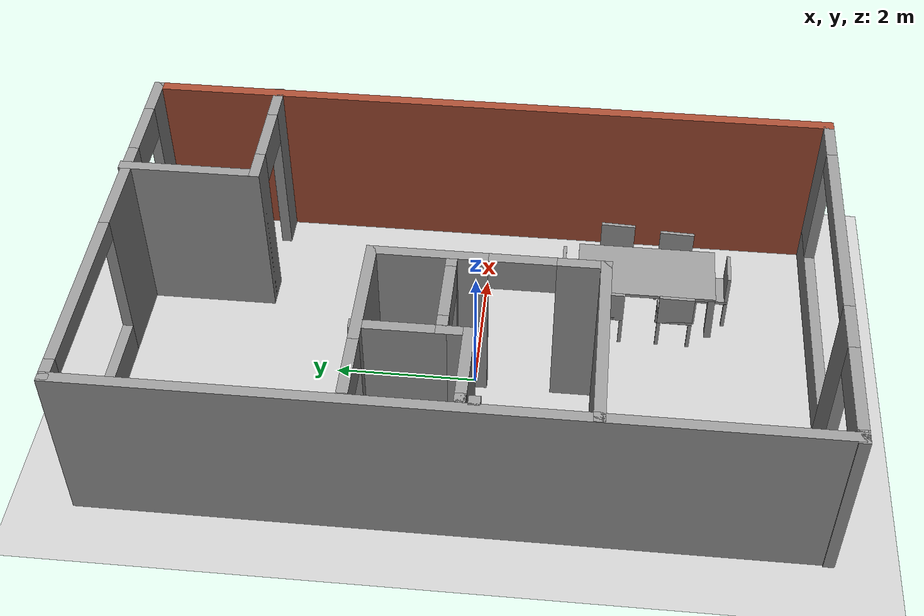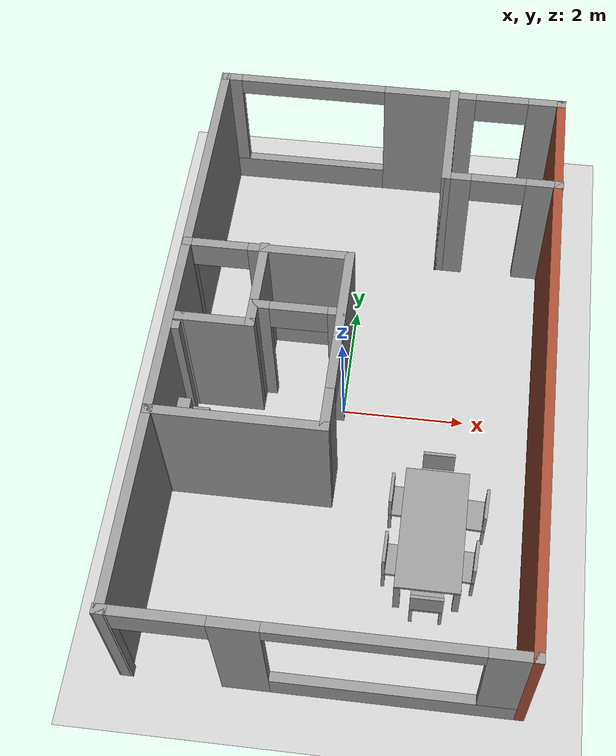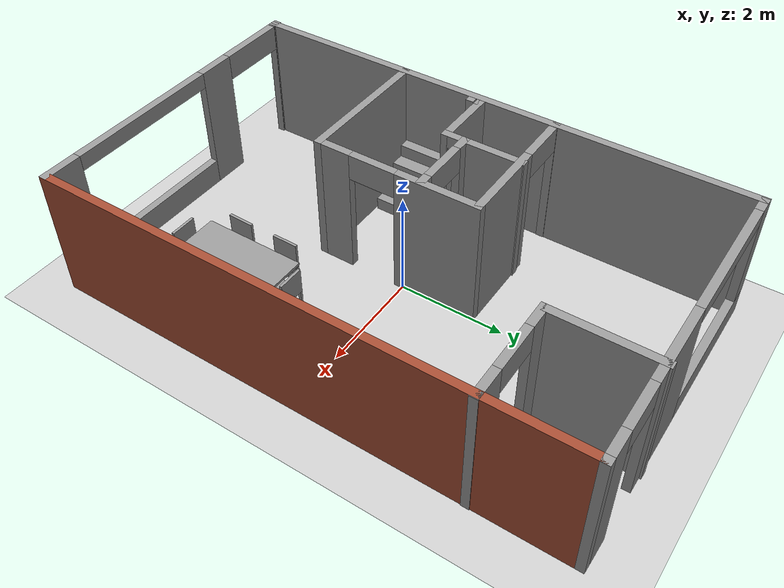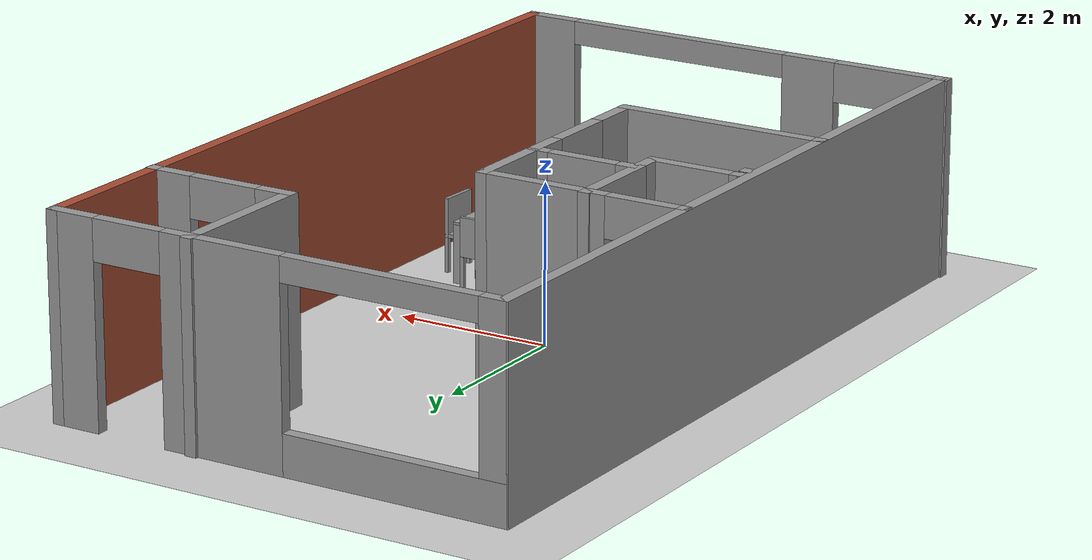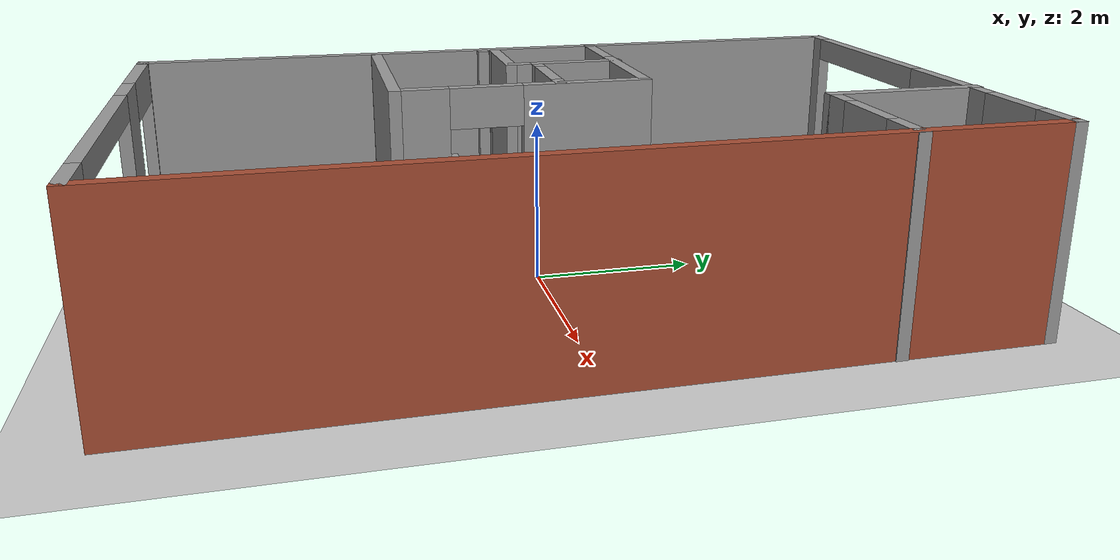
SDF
<sdf version="1.6">
 <world name="default">
  <light name="sun" type="directional">
   <pose>0 0 10 0 -0 0</pose>
   <diffuse>0.8 0.8 0.8 1</diffuse>
   <specular>0.2 0.2 0.2 1</specular>
   <attenuation>
    <range>1000</range>
    <constant>0.9</constant>
    <linear>0.01</linear>
    <quadratic>0.001</quadratic>
   </attenuation>
   <direction>-0.5 0.1 -0.9</direction>
  </light>
  <model name="ground_plane">
   <static>1</static>
   <link name="link">
    <collision name="collision">
     <geometry><plane><normal>0 0 1</normal><size>100 100</size></plane></geometry>
     <surface><friction><ode><mu>100</mu><mu2>50</mu2></ode></friction></surface>
    </collision>
    <visual name="visual">
     <cast_shadows>0</cast_shadows>
     <geometry><plane><normal>0 0 1</normal><size>100 100</size></plane></geometry>
     <material>
      <script><uri>file://media/materials/scripts/gazebo.material</uri><name>Gazebo/Grey</name></script>
     </material>
    </visual>
   </link>
  </model>
  <gravity>0 0 -9.8</gravity>
  <magnetic_field>6e-06 2.3e-05 -4.2e-05</magnetic_field>
  <atmosphere type="adiabatic"/>
  <physics name="default_physics" default="0" type="ode">
   <max_step_size>0.001</max_step_size>
   <real_time_factor>1</real_time_factor>
   <real_time_update_rate>1000</real_time_update_rate>
  </physics>
  <scene><ambient>0.4 0.4 0.4 1</ambient><background>0.7 0.7 0.7 1</background><shadows>1</shadows></scene>
  <spherical_coordinates>
   <surface_model>EARTH_WGS84</surface_model>
   <latitude_deg>0</latitude_deg>
   <longitude_deg>0</longitude_deg>
   <elevation>0</elevation>
   <heading_deg>0</heading_deg>
  </spherical_coordinates>
  <model name="Livingroomlab">
   <pose>0.248675 0.131128 0 0 -0 0</pose>
   <link name="Stairs_1">
    <visual name="Stairs_1_Visual_0">
     <pose>-1.93298 -1.24451 0.125 0 0 -1.5708</pose>
     <geometry><box><size>1 0.2765 0.25</size></box></geometry>
     <material>
      <script><uri>file://media/materials/scripts/gazebo.material</uri><name>Gazebo/Grey</name></script>
      <ambient>1 1 1 1</ambient>
     </material>
     <meta><layer>0</layer></meta>
    </visual>
    <collision name="Stairs_1_Collision_0">
     <geometry><box><size>1 0.2765 0.25</size></box></geometry>
     <pose>-1.93298 -1.24451 0.125 0 0 -1.5708</pose>
    </collision>
    <visual name="Stairs_1_Visual_1">
     <pose>-2.20948 -1.24451 0.375 0 0 -1.5708</pose>
     <geometry><box><size>1 0.2765 0.25</size></box></geometry>
     <material>
      <script><uri>file://media/materials/scripts/gazebo.material</uri><name>Gazebo/Grey</name></script>
      <ambient>1 1 1 1</ambient>
     </material>
     <meta><layer>0</layer></meta>
    </visual>
    <collision name="Stairs_1_Collision_1">
     <geometry><box><size>1 0.2765 0.25</size></box></geometry>
     <pose>-2.20948 -1.24451 0.375 0 0 -1.5708</pose>
    </collision>
    <visual name="Stairs_1_Visual_2">
     <pose>-2.48598 -1.24451 0.625 0 0 -1.5708</pose>
     <geometry><box><size>1 0.2765 0.25</size></box></geometry>
     <material>
      <script><uri>file://media/materials/scripts/gazebo.material</uri><name>Gazebo/Grey</name></script>
      <ambient>1 1 1 1</ambient>
     </material>
     <meta><layer>0</layer></meta>
    </visual>
    <collision name="Stairs_1_Collision_2">
     <geometry><box><size>1 0.2765 0.25</size></box></geometry>
     <pose>-2.48598 -1.24451 0.625 0 0 -1.5708</pose>
    </collision>
    <visual name="Stairs_1_Visual_3">
     <pose>-2.76248 -1.24451 0.875 0 0 -1.5708</pose>
     <geometry><box><size>1 0.2765 0.25</size></box></geometry>
     <material>
      <script><uri>file://media/materials/scripts/gazebo.material</uri><name>Gazebo/Grey</name></script>
      <ambient>1 1 1 1</ambient>
     </material>
     <meta><layer>0</layer></meta>
    </visual>
    <collision name="Stairs_1_Collision_3">
     <geometry><box><size>1 0.2765 0.25</size></box></geometry>
     <pose>-2.76248 -1.24451 0.875 0 0 -1.5708</pose>
    </collision>
   </link>
   <link name="Wall_10">
    <collision name="Wall_10_Collision">
     <geometry><box><size>0.15 0.15 2.5</size></box></geometry>
     <pose>0 0 1.25 0 -0 0</pose>
    </collision>
    <visual name="Wall_10_Visual">
     <pose>0 0 1.25 0 -0 0</pose>
     <geometry><box><size>0.15 0.15 2.5</size></box></geometry>
     <material>
      <script><uri>file://media/materials/scripts/gazebo.material</uri><name>Gazebo/Grey</name></script>
      <ambient>1 1 1 1</ambient>
     </material>
     <meta><layer>0</layer></meta>
    </visual>
    <pose>2.91851 4.90773 0 0 -0 0</pose>
   </link>
   <link name="Wall_15">
    <pose>0.016769 4.90773 0 0 -0 3.14159</pose>
    <visual name="Wall_15_Visual_0">
     <pose>-2.65996 0 1.25 0 -0 0</pose>
     <geometry><box><size>0.633556 0.15 2.5</size></box></geometry>
     <material>
      <script><uri>file://media/materials/scripts/gazebo.material</uri><name>Gazebo/Grey</name></script>
      <ambient>1 1 1 1</ambient>
     </material>
     <meta><layer>0</layer></meta>
    </visual>
    <collision name="Wall_15_Collision_0">
     <geometry><box><size>0.633556 0.15 2.5</size></box></geometry>
     <pose>-2.65996 0 1.25 0 -0 0</pose>
    </collision>
    <visual name="Wall_15_Visual_1">
     <pose>-0.65252 0 1.25 0 -0 0</pose>
     <geometry><box><size>1.58132 0.15 2.5</size></box></geometry>
     <material>
      <script><uri>file://media/materials/scripts/gazebo.material</uri><name>Gazebo/Grey</name></script>
      <ambient>1 1 1 1</ambient>
     </material>
     <meta><layer>0</layer></meta>
    </visual>
    <collision name="Wall_15_Collision_1">
     <geometry><box><size>1.58132 0.15 2.5</size></box></geometry>
     <pose>-0.65252 0 1.25 0 -0 0</pose>
    </collision>
    <visual name="Wall_15_Visual_2">
     <pose>1.55744 0 0.25 0 -0 0</pose>
     <geometry><box><size>2.8386 0.15 0.5</size></box></geometry>
     <material>
      <script><uri>file://media/materials/scripts/gazebo.material</uri><name>Gazebo/Grey</name></script>
      <ambient>1 1 1 1</ambient>
     </material>
     <meta><layer>0</layer></meta>
    </visual>
    <collision name="Wall_15_Collision_2">
     <geometry><box><size>2.8386 0.15 0.5</size></box></geometry>
     <pose>1.55744 0 0.25 0 -0 0</pose>
    </collision>
    <visual name="Wall_15_Visual_3">
     <pose>2.80744 0 1.5 0 -0 0</pose>
     <geometry><box><size>0.338597 0.15 2</size></box></geometry>
     <material>
      <script><uri>file://media/materials/scripts/gazebo.material</uri><name>Gazebo/Grey</name></script>
      <ambient>1 1 1 1</ambient>
     </material>
     <meta><layer>0</layer></meta>
    </visual>
    <collision name="Wall_15_Collision_3">
     <geometry><box><size>0.338597 0.15 2</size></box></geometry>
     <pose>2.80744 0 1.5 0 -0 0</pose>
    </collision>
    <visual name="Wall_15_Visual_4">
     <pose>-1.89318 0 2.25 0 -0 0</pose>
     <geometry><box><size>0.9 0.15 0.5</size></box></geometry>
     <material>
      <script><uri>file://media/materials/scripts/gazebo.material</uri><name>Gazebo/Grey</name></script>
      <ambient>1 1 1 1</ambient>
     </material>
     <meta><layer>0</layer></meta>
    </visual>
    <collision name="Wall_15_Collision_4">
     <geometry><box><size>0.9 0.15 0.5</size></box></geometry>
     <pose>-1.89318 0 2.25 0 -0 0</pose>
    </collision>
    <visual name="Wall_15_Visual_5">
     <pose>1.38814 0 2.35 0 -0 0</pose>
     <geometry><box><size>2.5 0.15 0.3</size></box></geometry>
     <material>
      <script><uri>file://media/materials/scripts/gazebo.material</uri><name>Gazebo/Grey</name></script>
      <ambient>1 1 1 1</ambient>
     </material>
     <meta><layer>0</layer></meta>
    </visual>
    <collision name="Wall_15_Collision_5">
     <geometry><box><size>2.5 0.15 0.3</size></box></geometry>
     <pose>1.38814 0 2.35 0 -0 0</pose>
    </collision>
   </link>
   <link name="Wall_16">
    <collision name="Wall_16_Collision">
     <geometry><box><size>10 0.15 2.5</size></box></geometry>
     <pose>0 0 1.25 0 -0 0</pose>
    </collision>
    <visual name="Wall_16_Visual">
     <pose>0 0 1.25 0 -0 0</pose>
     <geometry><box><size>10 0.15 2.5</size></box></geometry>
     <material>
      <script><uri>file://media/materials/scripts/gazebo.material</uri><name>Gazebo/Grey</name></script>
      <ambient>1 1 1 1</ambient>
     </material>
     <meta><layer>0</layer></meta>
    </visual>
    <pose>-2.90823 -0.017274 0 0 0 -1.5708</pose>
   </link>
   <link name="Wall_17">
    <collision name="Wall_17_Collision">
     <geometry><box><size>0.15 0.15 2.5</size></box></geometry>
     <pose>0 0 1.25 0 -0 0</pose>
    </collision>
    <visual name="Wall_17_Visual">
     <pose>0 0 1.25 0 -0 0</pose>
     <geometry><box><size>0.15 0.15 2.5</size></box></geometry>
     <material>
      <script><uri>file://media/materials/scripts/gazebo.material</uri><name>Gazebo/Grey</name></script>
      <ambient>1 1 1 1</ambient>
     </material>
     <meta><layer>0</layer></meta>
    </visual>
    <pose>-2.88497 -4.94227 0 0 -0 0</pose>
   </link>
   <link name="Wall_19">
    <collision name="Wall_19_Collision">
     <geometry><box><size>2 0.15 2.5</size></box></geometry>
     <pose>0 0 1.25 0 -0 0</pose>
    </collision>
    <visual name="Wall_19_Visual">
     <pose>0 0 1.25 0 -0 0</pose>
     <geometry><box><size>2 0.15 2.5</size></box></geometry>
     <material>
      <script><uri>file://media/materials/scripts/gazebo.material</uri><name>Gazebo/Grey</name></script>
      <ambient>1 1 1 1</ambient>
     </material>
     <meta><layer>0</layer></meta>
    </visual>
    <pose>1.08149 4.01727 0 0 0 -1.5708</pose>
   </link>
   <link name="Wall_20">
    <pose>2.00649 3.09227 0 0 -0 0</pose>
    <visual name="Wall_20_Visual_0">
     <pose>-0.756805 0 1.25 0 -0 0</pose>
     <geometry><box><size>0.48639 0.15 2.5</size></box></geometry>
     <material>
      <script><uri>file://media/materials/scripts/gazebo.material</uri><name>Gazebo/Grey</name></script>
      <ambient>1 1 1 1</ambient>
     </material>
     <meta><layer>0</layer></meta>
    </visual>
    <collision name="Wall_20_Collision_0">
     <geometry><box><size>0.48639 0.15 2.5</size></box></geometry>
     <pose>-0.756805 0 1.25 0 -0 0</pose>
    </collision>
    <visual name="Wall_20_Visual_1">
     <pose>0.693195 0 1.25 0 -0 0</pose>
     <geometry><box><size>0.61361 0.15 2.5</size></box></geometry>
     <material>
      <script><uri>file://media/materials/scripts/gazebo.material</uri><name>Gazebo/Grey</name></script>
      <ambient>1 1 1 1</ambient>
     </material>
     <meta><layer>0</layer></meta>
    </visual>
    <collision name="Wall_20_Collision_1">
     <geometry><box><size>0.61361 0.15 2.5</size></box></geometry>
     <pose>0.693195 0 1.25 0 -0 0</pose>
    </collision>
    <visual name="Wall_20_Visual_2">
     <pose>-0.06361 0 2.25 0 -0 0</pose>
     <geometry><box><size>0.9 0.15 0.5</size></box></geometry>
     <material>
      <script><uri>file://media/materials/scripts/gazebo.material</uri><name>Gazebo/Grey</name></script>
      <ambient>1 1 1 1</ambient>
     </material>
     <meta><layer>0</layer></meta>
    </visual>
    <collision name="Wall_20_Collision_2">
     <geometry><box><size>0.9 0.15 0.5</size></box></geometry>
     <pose>-0.06361 0 2.25 0 -0 0</pose>
    </collision>
   </link>
   <link name="Wall_21">
    <collision name="Wall_21_Collision">
     <geometry><box><size>0.15 0.15 2.5</size></box></geometry>
     <pose>0 0 1.25 0 -0 0</pose>
    </collision>
    <visual name="Wall_21_Visual">
     <pose>0 0 1.25 0 -0 0</pose>
     <geometry><box><size>0.15 0.15 2.5</size></box></geometry>
     <material>
      <script><uri>file://media/materials/scripts/gazebo.material</uri><name>Gazebo/Grey</name></script>
      <ambient>1 1 1 1</ambient>
     </material>
     <meta><layer>0</layer></meta>
    </visual>
    <pose>2.93149 3.09227 0 0 -0 0</pose>
   </link>
   <link name="Wall_23">
    <pose>-1.59731 1.2506 0 0 -0 0</pose>
    <visual name="Wall_23_Visual_0">
     <pose>-1.29946 0 1.25 0 -0 0</pose>
     <geometry><box><size>0.151074 0.15 2.5</size></box></geometry>
     <material>
      <script><uri>file://media/materials/scripts/gazebo.material</uri><name>Gazebo/Grey</name></script>
      <ambient>1 1 1 1</ambient>
     </material>
     <meta><layer>0</layer></meta>
    </visual>
    <collision name="Wall_23_Collision_0">
     <geometry><box><size>0.151074 0.15 2.5</size></box></geometry>
     <pose>-1.29946 0 1.25 0 -0 0</pose>
    </collision>
    <visual name="Wall_23_Visual_1">
     <pose>0.525537 0 1.25 0 -0 0</pose>
     <geometry><box><size>1.69893 0.15 2.5</size></box></geometry>
     <material>
      <script><uri>file://media/materials/scripts/gazebo.material</uri><name>Gazebo/Grey</name></script>
      <ambient>1 1 1 1</ambient>
     </material>
     <meta><layer>0</layer></meta>
    </visual>
    <collision name="Wall_23_Collision_1">
     <geometry><box><size>1.69893 0.15 2.5</size></box></geometry>
     <pose>0.525537 0 1.25 0 -0 0</pose>
    </collision>
    <visual name="Wall_23_Visual_2">
     <pose>-0.773926 0 2.25 0 -0 0</pose>
     <geometry><box><size>0.9 0.15 0.5</size></box></geometry>
     <material>
      <script><uri>file://media/materials/scripts/gazebo.material</uri><name>Gazebo/Grey</name></script>
      <ambient>1 1 1 1</ambient>
     </material>
     <meta><layer>0</layer></meta>
    </visual>
    <collision name="Wall_23_Collision_2">
     <geometry><box><size>0.9 0.15 0.5</size></box></geometry>
     <pose>-0.773926 0 2.25 0 -0 0</pose>
    </collision>
   </link>
   <link name="Wall_26">
    <collision name="Wall_26_Collision">
     <geometry><box><size>0.15 0.15 2.5</size></box></geometry>
     <pose>0 0 1.25 0 -0 0</pose>
    </collision>
    <visual name="Wall_26_Visual">
     <pose>0 0 1.25 0 -0 0</pose>
     <geometry><box><size>0.15 0.15 2.5</size></box></geometry>
     <material>
      <script><uri>file://media/materials/scripts/gazebo.material</uri><name>Gazebo/Grey</name></script>
      <ambient>1 1 1 1</ambient>
     </material>
     <meta><layer>0</layer></meta>
    </visual>
    <pose>-2.78426 -0.349398 0 0 -0 0</pose>
   </link>
   <link name="Wall_28">
    <pose>-0.297309 -0.299398 0 0 0 -1.5708</pose>
    <visual name="Wall_28_Visual_0">
     <pose>-0.81151 0 1.25 0 -0 0</pose>
     <geometry><box><size>1.62698 0.15 2.5</size></box></geometry>
     <material>
      <script><uri>file://media/materials/scripts/gazebo.material</uri><name>Gazebo/Grey</name></script>
      <ambient>1 1 1 1</ambient>
     </material>
     <meta><layer>0</layer></meta>
    </visual>
    <collision name="Wall_28_Collision_0">
     <geometry><box><size>1.62698 0.15 2.5</size></box></geometry>
     <pose>-0.81151 0 1.25 0 -0 0</pose>
    </collision>
    <visual name="Wall_28_Visual_1">
     <pose>1.26349 0 1.25 0 -0 0</pose>
     <geometry><box><size>0.72302 0.15 2.5</size></box></geometry>
     <material>
      <script><uri>file://media/materials/scripts/gazebo.material</uri><name>Gazebo/Grey</name></script>
      <ambient>1 1 1 1</ambient>
     </material>
     <meta><layer>0</layer></meta>
    </visual>
    <collision name="Wall_28_Collision_1">
     <geometry><box><size>0.72302 0.15 2.5</size></box></geometry>
     <pose>1.26349 0 1.25 0 -0 0</pose>
    </collision>
    <visual name="Wall_28_Visual_2">
     <pose>0.45198 0 2.25 0 -0 0</pose>
     <geometry><box><size>0.9 0.15 0.5</size></box></geometry>
     <material>
      <script><uri>file://media/materials/scripts/gazebo.material</uri><name>Gazebo/Grey</name></script>
      <ambient>1 1 1 1</ambient>
     </material>
     <meta><layer>0</layer></meta>
    </visual>
    <collision name="Wall_28_Collision_2">
     <geometry><box><size>0.9 0.15 0.5</size></box></geometry>
     <pose>0.45198 0 2.25 0 -0 0</pose>
    </collision>
   </link>
   <link name="Wall_29">
    <collision name="Wall_29_Collision">
     <geometry><box><size>2.75 0.15 2.5</size></box></geometry>
     <pose>0 0 1.25 0 -0 0</pose>
    </collision>
    <visual name="Wall_29_Visual">
     <pose>0 0 1.25 0 -0 0</pose>
     <geometry><box><size>2.75 0.15 2.5</size></box></geometry>
     <material>
      <script><uri>file://media/materials/scripts/gazebo.material</uri><name>Gazebo/Grey</name></script>
      <ambient>1 1 1 1</ambient>
     </material>
     <meta><layer>0</layer></meta>
    </visual>
    <pose>-1.59731 -1.8494 0 0 -0 3.14159</pose>
   </link>
   <link name="Wall_30">
    <collision name="Wall_30_Collision">
     <geometry><box><size>0.15 0.15 2.5</size></box></geometry>
     <pose>0 0 1.25 0 -0 0</pose>
    </collision>
    <visual name="Wall_30_Visual">
     <pose>0 0 1.25 0 -0 0</pose>
     <geometry><box><size>0.15 0.15 2.5</size></box></geometry>
     <material>
      <script><uri>file://media/materials/scripts/gazebo.material</uri><name>Gazebo/Grey</name></script>
      <ambient>1 1 1 1</ambient>
     </material>
     <meta><layer>0</layer></meta>
    </visual>
    <pose>-2.89731 -1.8494 0 0 -0 0</pose>
   </link>
   <link name="Wall_32">
    <collision name="Wall_32_Collision">
     <geometry><box><size>1.25 0.15 2.5</size></box></geometry>
     <pose>0 0 1.25 0 -0 0</pose>
    </collision>
    <visual name="Wall_32_Visual">
     <pose>0 0 1.25 0 -0 0</pose>
     <geometry><box><size>1.25 0.15 2.5</size></box></geometry>
     <material>
      <script><uri>file://media/materials/scripts/gazebo.material</uri><name>Gazebo/Grey</name></script>
      <ambient>1 1 1 1</ambient>
     </material>
     <meta><layer>0</layer></meta>
    </visual>
    <pose>-1.65945 0.725303 0 0 0 -1.5708</pose>
   </link>
   <link name="Wall_33">
    <pose>-0.984448 0.175303 0 0 -0 0</pose>
    <visual name="Wall_33_Visual_0">
     <pose>-0.587699 0 1.25 0 -0 0</pose>
     <geometry><box><size>0.324602 0.15 2.5</size></box></geometry>
     <material>
      <script><uri>file://media/materials/scripts/gazebo.material</uri><name>Gazebo/Grey</name></script>
      <ambient>1 1 1 1</ambient>
     </material>
     <meta><layer>0</layer></meta>
    </visual>
    <collision name="Wall_33_Collision_0">
     <geometry><box><size>0.324602 0.15 2.5</size></box></geometry>
     <pose>-0.587699 0 1.25 0 -0 0</pose>
    </collision>
    <visual name="Wall_33_Visual_1">
     <pose>0.612301 0 1.25 0 -0 0</pose>
     <geometry><box><size>0.275398 0.15 2.5</size></box></geometry>
     <material>
      <script><uri>file://media/materials/scripts/gazebo.material</uri><name>Gazebo/Grey</name></script>
      <ambient>1 1 1 1</ambient>
     </material>
     <meta><layer>0</layer></meta>
    </visual>
    <collision name="Wall_33_Collision_1">
     <geometry><box><size>0.275398 0.15 2.5</size></box></geometry>
     <pose>0.612301 0 1.25 0 -0 0</pose>
    </collision>
    <visual name="Wall_33_Visual_2">
     <pose>0.024602 0 2.25 0 -0 0</pose>
     <geometry><box><size>0.9 0.15 0.5</size></box></geometry>
     <material>
      <script><uri>file://media/materials/scripts/gazebo.material</uri><name>Gazebo/Grey</name></script>
      <ambient>1 1 1 1</ambient>
     </material>
     <meta><layer>0</layer></meta>
    </visual>
    <collision name="Wall_33_Collision_2">
     <geometry><box><size>0.9 0.15 0.5</size></box></geometry>
     <pose>0.024602 0 2.25 0 -0 0</pose>
    </collision>
   </link>
   <link name="Wall_35">
    <collision name="Wall_35_Collision">
     <geometry><box><size>0.5 0.15 2.5</size></box></geometry>
     <pose>0 0 1.25 0 -0 0</pose>
    </collision>
    <visual name="Wall_35_Visual">
     <pose>0 0 1.25 0 -0 0</pose>
     <geometry><box><size>0.5 0.15 2.5</size></box></geometry>
     <material>
      <script><uri>file://media/materials/scripts/gazebo.material</uri><name>Gazebo/Grey</name></script>
      <ambient>1 1 1 1</ambient>
     </material>
     <meta><layer>0</layer></meta>
    </visual>
    <pose>-1.65945 0.000303 0 0 0 -1.5708</pose>
   </link>
   <link name="Wall_36">
    <collision name="Wall_36_Collision">
     <geometry><box><size>1.25 0.15 2.5</size></box></geometry>
     <pose>0 0 1.25 0 -0 0</pose>
    </collision>
    <visual name="Wall_36_Visual">
     <pose>0 0 1.25 0 -0 0</pose>
     <geometry><box><size>1.25 0.15 2.5</size></box></geometry>
     <material>
      <script><uri>file://media/materials/scripts/gazebo.material</uri><name>Gazebo/Grey</name></script>
      <ambient>1 1 1 1</ambient>
     </material>
     <meta><layer>0</layer></meta>
    </visual>
    <pose>-2.20945 -0.174697 0 0 -0 3.14159</pose>
   </link>
   <link name="Wall_37">
    <collision name="Wall_37_Collision">
     <geometry><box><size>0.15 0.15 2.5</size></box></geometry>
     <pose>0 0 1.25 0 -0 0</pose>
    </collision>
    <visual name="Wall_37_Visual">
     <pose>0 0 1.25 0 -0 0</pose>
     <geometry><box><size>0.15 0.15 2.5</size></box></geometry>
     <material>
      <script><uri>file://media/materials/scripts/gazebo.material</uri><name>Gazebo/Grey</name></script>
      <ambient>1 1 1 1</ambient>
     </material>
     <meta><layer>0</layer></meta>
    </visual>
    <pose>-2.75945 -0.174697 0 0 -0 0</pose>
   </link>
   <link name="Wall_4">
    <pose>-0.006493 -4.94227 0 0 -0 0</pose>
    <visual name="Wall_4_Visual_0">
     <pose>-2.8964 0 1.25 0 -0 0</pose>
     <geometry><box><size>0.207193 0.15 2.5</size></box></geometry>
     <material>
      <script><uri>file://media/materials/scripts/gazebo.material</uri><name>Gazebo/Grey</name></script>
      <ambient>1 1 1 1</ambient>
     </material>
     <meta><layer>0</layer></meta>
    </visual>
    <collision name="Wall_4_Collision_0">
     <geometry><box><size>0.207193 0.15 2.5</size></box></geometry>
     <pose>-2.8964 0 1.25 0 -0 0</pose>
    </collision>
    <visual name="Wall_4_Visual_1">
     <pose>-1.0981 0 1.25 0 -0 0</pose>
     <geometry><box><size>0.722472 0.15 2.5</size></box></geometry>
     <material>
      <script><uri>file://media/materials/scripts/gazebo.material</uri><name>Gazebo/Grey</name></script>
      <ambient>1 1 1 1</ambient>
     </material>
     <meta><layer>0</layer></meta>
    </visual>
    <collision name="Wall_4_Collision_1">
     <geometry><box><size>0.722472 0.15 2.5</size></box></geometry>
     <pose>-1.0981 0 1.25 0 -0 0</pose>
    </collision>
    <visual name="Wall_4_Visual_2">
     <pose>1.13157 0 0.25 0 -0 0</pose>
     <geometry><box><size>3.73686 0.15 0.5</size></box></geometry>
     <material>
      <script><uri>file://media/materials/scripts/gazebo.material</uri><name>Gazebo/Grey</name></script>
      <ambient>1 1 1 1</ambient>
     </material>
     <meta><layer>0</layer></meta>
    </visual>
    <collision name="Wall_4_Collision_2">
     <geometry><box><size>3.73686 0.15 0.5</size></box></geometry>
     <pose>1.13157 0 0.25 0 -0 0</pose>
    </collision>
    <visual name="Wall_4_Visual_3">
     <pose>2.63157 0 1.5 0 -0 0</pose>
     <geometry><box><size>0.736863 0.15 2</size></box></geometry>
     <material>
      <script><uri>file://media/materials/scripts/gazebo.material</uri><name>Gazebo/Grey</name></script>
      <ambient>1 1 1 1</ambient>
     </material>
     <meta><layer>0</layer></meta>
    </visual>
    <collision name="Wall_4_Collision_3">
     <geometry><box><size>0.736863 0.15 2</size></box></geometry>
     <pose>2.63157 0 1.5 0 -0 0</pose>
    </collision>
    <visual name="Wall_4_Visual_4">
     <pose>-2.12607 0 2.25 0 -0 0</pose>
     <geometry><box><size>1.33347 0.15 0.5</size></box></geometry>
     <material>
      <script><uri>file://media/materials/scripts/gazebo.material</uri><name>Gazebo/Grey</name></script>
      <ambient>1 1 1 1</ambient>
     </material>
     <meta><layer>0</layer></meta>
    </visual>
    <collision name="Wall_4_Collision_4">
     <geometry><box><size>1.33347 0.15 0.5</size></box></geometry>
     <pose>-2.12607 0 2.25 0 -0 0</pose>
    </collision>
    <visual name="Wall_4_Visual_5">
     <pose>0.763137 0 2.35 0 -0 0</pose>
     <geometry><box><size>3 0.15 0.3</size></box></geometry>
     <material>
      <script><uri>file://media/materials/scripts/gazebo.material</uri><name>Gazebo/Grey</name></script>
      <ambient>1 1 1 1</ambient>
     </material>
     <meta><layer>0</layer></meta>
    </visual>
    <collision name="Wall_4_Collision_5">
     <geometry><box><size>3 0.15 0.3</size></box></geometry>
     <pose>0.763137 0 2.35 0 -0 0</pose>
    </collision>
   </link>
   <link name="Wall_9">
    <collision name="Wall_9_Collision">
     <geometry><box><size>10 0.15 2.5</size></box></geometry>
     <pose>0 0 1.25 0 -0 0</pose>
    </collision>
    <visual name="Wall_9_Visual">
     <pose>0 0 1.25 0 -0 0</pose>
     <geometry><box><size>10 0.15 2.5</size></box></geometry>
     <material>
      <script><uri>file://media/materials/scripts/gazebo.material</uri><name>Gazebo/Bricks</name></script>
      <ambient>0.996078 0.47451 0.0196078 1</ambient>
     </material>
     <meta><layer>0</layer></meta>
    </visual>
    <pose>2.91851 -0.017274 0 0 -0 1.5708</pose>
   </link>
   <static>1</static>
  </model>
  <model name="table">
   <link name="link_2">
    <pose>-0.000914 0.01077 -0.287764 0 -0 0</pose>
    <inertial>
     <mass>1</mass>
     <inertia>
      <ixx>0.166667</ixx>
      <ixy>0</ixy>
      <ixz>0</ixz>
      <iyy>0.166667</iyy>
      <iyz>0</iyz>
      <izz>0.166667</izz>
     </inertia>
    </inertial>
    <visual name="visual">
     <pose>0 0 0.75 0 -0 0</pose>
     <geometry><box><size>1 2 0.05</size></box></geometry>
     <material>
      <lighting>1</lighting>
      <script><uri>file://media/materials/scripts/gazebo.material</uri><name>Gazebo/Grey</name></script>
      <ambient>0.3 0.3 0.3 1</ambient>
      <diffuse>0.7 0.7 0.7 1</diffuse>
      <specular>0.01 0.01 0.01 1</specular>
      <emissive>0 0 0 1</emissive>
      <shader type="vertex"><normal_map>__default__</normal_map></shader>
     </material>
    </visual>
    <collision name="collision">
     <pose>0 0 0.75 0 -0 0</pose>
     <geometry><box><size>1 2 0.05</size></box></geometry>
     <surface>
      <friction>
       <ode><mu>1</mu><mu2>1</mu2><fdir1>0 0 0</fdir1><slip1>0</slip1><slip2>0</slip2></ode>
       <torsional>
        <coefficient>1</coefficient>
        <patch_radius>0</patch_radius>
        <surface_radius>0</surface_radius>
        <use_patch_radius>1</use_patch_radius>
        <ode><slip>0</slip></ode>
       </torsional>
      </friction>
      <bounce><restitution_coefficient>0</restitution_coefficient><threshold>1e+06</threshold></bounce>
      <contact>
       <collide_without_contact>0</collide_without_contact>
       <collide_without_contact_bitmask>1</collide_without_contact_bitmask>
       <collide_bitmask>1</collide_bitmask>
       <ode>
        <soft_cfm>0</soft_cfm>
        <soft_erp>0.2</soft_erp>
        <kp>1e+13</kp>
        <kd>1</kd>
        <max_vel>0.01</max_vel>
        <min_depth>0</min_depth>
       </ode>
       <bullet>
        <split_impulse>1</split_impulse>
        <split_impulse_penetration_threshold>-0.01</split_impulse_penetration_threshold>
        <soft_cfm>0</soft_cfm>
        <soft_erp>0.2</soft_erp>
        <kp>1e+13</kp>
        <kd>1</kd>
       </bullet>
      </contact>
     </surface>
    </collision>
   </link>
   <link name="link_3">
    <pose>-0.450914 0.87078 0.080236 0 -0 0</pose>
    <inertial>
     <mass>1</mass>
     <inertia>
      <ixx>0.166667</ixx>
      <ixy>0</ixy>
      <ixz>0</ixz>
      <iyy>0.166667</iyy>
      <iyz>0</iyz>
      <izz>0.166667</izz>
     </inertia>
    </inertial>
    <visual name="visual">
     <geometry><box><size>0.1 0.1 0.75</size></box></geometry>
     <material>
      <lighting>1</lighting>
      <script><uri>file://media/materials/scripts/gazebo.material</uri><name>Gazebo/Grey</name></script>
      <ambient>0.3 0.3 0.3 1</ambient>
      <diffuse>0.7 0.7 0.7 1</diffuse>
      <specular>0.01 0.01 0.01 1</specular>
      <emissive>0 0 0 1</emissive>
      <shader type="vertex"><normal_map>__default__</normal_map></shader>
     </material>
    </visual>
    <collision name="collision">
     <geometry><box><size>0.1 0.1 0.75</size></box></geometry>
     <surface>
      <friction>
       <ode><mu>1</mu><mu2>1</mu2><fdir1>0 0 0</fdir1><slip1>0</slip1><slip2>0</slip2></ode>
       <torsional>
        <coefficient>1</coefficient>
        <patch_radius>0</patch_radius>
        <surface_radius>0</surface_radius>
        <use_patch_radius>1</use_patch_radius>
        <ode><slip>0</slip></ode>
       </torsional>
      </friction>
      <bounce><restitution_coefficient>0</restitution_coefficient><threshold>1e+06</threshold></bounce>
      <contact>
       <collide_without_contact>0</collide_without_contact>
       <collide_without_contact_bitmask>1</collide_without_contact_bitmask>
       <collide_bitmask>1</collide_bitmask>
       <ode>
        <soft_cfm>0</soft_cfm>
        <soft_erp>0.2</soft_erp>
        <kp>1e+13</kp>
        <kd>1</kd>
        <max_vel>0.01</max_vel>
        <min_depth>0</min_depth>
       </ode>
       <bullet>
        <split_impulse>1</split_impulse>
        <split_impulse_penetration_threshold>-0.01</split_impulse_penetration_threshold>
        <soft_cfm>0</soft_cfm>
        <soft_erp>0.2</soft_erp>
        <kp>1e+13</kp>
        <kd>1</kd>
       </bullet>
      </contact>
     </surface>
    </collision>
   </link>
   <link name="link_3_clone_0">
    <pose>0.45366 -0.903088 0.047057 0 -0 0</pose>
    <inertial>
     <mass>1</mass>
     <inertia>
      <ixx>0.166667</ixx>
      <ixy>0</ixy>
      <ixz>0</ixz>
      <iyy>0.166667</iyy>
      <iyz>0</iyz>
      <izz>0.166667</izz>
     </inertia>
    </inertial>
    <visual name="visual">
     <geometry><box><size>0.1 0.1 0.75</size></box></geometry>
     <material>
      <lighting>1</lighting>
      <script><uri>file://media/materials/scripts/gazebo.material</uri><name>Gazebo/Grey</name></script>
      <ambient>0.3 0.3 0.3 1</ambient>
      <diffuse>0.7 0.7 0.7 1</diffuse>
      <specular>0.01 0.01 0.01 1</specular>
      <emissive>0 0 0 1</emissive>
      <shader type="vertex"><normal_map>__default__</normal_map></shader>
     </material>
    </visual>
    <collision name="collision">
     <geometry><box><size>0.1 0.1 0.75</size></box></geometry>
     <surface>
      <friction>
       <ode><mu>1</mu><mu2>1</mu2><fdir1>0 0 0</fdir1><slip1>0</slip1><slip2>0</slip2></ode>
       <torsional>
        <coefficient>1</coefficient>
        <patch_radius>0</patch_radius>
        <surface_radius>0</surface_radius>
        <use_patch_radius>1</use_patch_radius>
        <ode><slip>0</slip></ode>
       </torsional>
      </friction>
      <bounce><restitution_coefficient>0</restitution_coefficient><threshold>1e+06</threshold></bounce>
      <contact>
       <collide_without_contact>0</collide_without_contact>
       <collide_without_contact_bitmask>1</collide_without_contact_bitmask>
       <collide_bitmask>1</collide_bitmask>
       <ode>
        <soft_cfm>0</soft_cfm>
        <soft_erp>0.2</soft_erp>
        <kp>1e+13</kp>
        <kd>1</kd>
        <max_vel>0.01</max_vel>
        <min_depth>0</min_depth>
       </ode>
       <bullet>
        <split_impulse>1</split_impulse>
        <split_impulse_penetration_threshold>-0.01</split_impulse_penetration_threshold>
        <soft_cfm>0</soft_cfm>
        <soft_erp>0.2</soft_erp>
        <kp>1e+13</kp>
        <kd>1</kd>
       </bullet>
      </contact>
     </surface>
    </collision>
   </link>
   <link name="link_3_clone_0_clone">
    <pose>-0.450914 -0.93923 0.080236 -0.02 0 0</pose>
    <inertial>
     <mass>1</mass>
     <inertia>
      <ixx>0.166667</ixx>
      <ixy>0</ixy>
      <ixz>0</ixz>
      <iyy>0.166667</iyy>
      <iyz>0</iyz>
      <izz>0.166667</izz>
     </inertia>
    </inertial>
    <visual name="visual">
     <geometry><box><size>0.1 0.1 0.75</size></box></geometry>
     <material>
      <lighting>1</lighting>
      <script><uri>file://media/materials/scripts/gazebo.material</uri><name>Gazebo/Grey</name></script>
      <ambient>0.3 0.3 0.3 1</ambient>
      <diffuse>0.7 0.7 0.7 1</diffuse>
      <specular>0.01 0.01 0.01 1</specular>
      <emissive>0 0 0 1</emissive>
      <shader type="vertex"><normal_map>__default__</normal_map></shader>
     </material>
    </visual>
    <collision name="collision">
     <geometry><box><size>0.1 0.1 0.75</size></box></geometry>
     <surface>
      <friction>
       <ode><mu>1</mu><mu2>1</mu2><fdir1>0 0 0</fdir1><slip1>0</slip1><slip2>0</slip2></ode>
       <torsional>
        <coefficient>1</coefficient>
        <patch_radius>0</patch_radius>
        <surface_radius>0</surface_radius>
        <use_patch_radius>1</use_patch_radius>
        <ode><slip>0</slip></ode>
       </torsional>
      </friction>
      <bounce><restitution_coefficient>0</restitution_coefficient><threshold>1e+06</threshold></bounce>
      <contact>
       <collide_without_contact>0</collide_without_contact>
       <collide_without_contact_bitmask>1</collide_without_contact_bitmask>
       <collide_bitmask>1</collide_bitmask>
       <ode>
        <soft_cfm>0</soft_cfm>
        <soft_erp>0.2</soft_erp>
        <kp>1e+13</kp>
        <kd>1</kd>
        <max_vel>0.01</max_vel>
        <min_depth>0</min_depth>
       </ode>
       <bullet>
        <split_impulse>1</split_impulse>
        <split_impulse_penetration_threshold>-0.01</split_impulse_penetration_threshold>
        <soft_cfm>0</soft_cfm>
        <soft_erp>0.2</soft_erp>
        <kp>1e+13</kp>
        <kd>1</kd>
       </bullet>
      </contact>
     </surface>
    </collision>
   </link>
   <link name="link_3_clone_1">
    <pose>0.449089 0.960775 0.080236 0 -0 0</pose>
    <inertial>
     <mass>1</mass>
     <inertia>
      <ixx>0.166667</ixx>
      <ixy>0</ixy>
      <ixz>0</ixz>
      <iyy>0.166667</iyy>
      <iyz>0</iyz>
      <izz>0.166667</izz>
     </inertia>
    </inertial>
    <visual name="visual">
     <geometry><box><size>0.1 0.1 0.75</size></box></geometry>
     <material>
      <lighting>1</lighting>
      <script><uri>file://media/materials/scripts/gazebo.material</uri><name>Gazebo/Grey</name></script>
      <ambient>0.3 0.3 0.3 1</ambient>
      <diffuse>0.7 0.7 0.7 1</diffuse>
      <specular>0.01 0.01 0.01 1</specular>
      <emissive>0 0 0 1</emissive>
      <shader type="vertex"><normal_map>__default__</normal_map></shader>
     </material>
    </visual>
    <collision name="collision">
     <geometry><box><size>0.1 0.1 0.75</size></box></geometry>
     <surface>
      <friction>
       <ode><mu>1</mu><mu2>1</mu2><fdir1>0 0 0</fdir1><slip1>0</slip1><slip2>0</slip2></ode>
       <torsional>
        <coefficient>1</coefficient>
        <patch_radius>0</patch_radius>
        <surface_radius>0</surface_radius>
        <use_patch_radius>1</use_patch_radius>
        <ode><slip>0</slip></ode>
       </torsional>
      </friction>
      <bounce><restitution_coefficient>0</restitution_coefficient><threshold>1e+06</threshold></bounce>
      <contact>
       <collide_without_contact>0</collide_without_contact>
       <collide_without_contact_bitmask>1</collide_without_contact_bitmask>
       <collide_bitmask>1</collide_bitmask>
       <ode>
        <soft_cfm>0</soft_cfm>
        <soft_erp>0.2</soft_erp>
        <kp>1e+13</kp>
        <kd>1</kd>
        <max_vel>0.01</max_vel>
        <min_depth>0</min_depth>
       </ode>
       <bullet>
        <split_impulse>1</split_impulse>
        <split_impulse_penetration_threshold>-0.01</split_impulse_penetration_threshold>
        <soft_cfm>0</soft_cfm>
        <soft_erp>0.2</soft_erp>
        <kp>1e+13</kp>
        <kd>1</kd>
       </bullet>
      </contact>
     </surface>
    </collision>
   </link>
   <joint name="link_2_JOINT_10" type="fixed">
    <parent>link_2</parent>
    <child>link_3_clone_1</child>
    <physics>
     <ode><limit><cfm>0</cfm><erp>0.2</erp></limit><suspension><cfm>0</cfm><erp>0.2</erp></suspension></ode>
    </physics>
   </joint>
   <joint name="link_2_JOINT_11" type="fixed">
    <parent>link_2</parent>
    <child>link_3</child>
    <physics>
     <ode><limit><cfm>0</cfm><erp>0.2</erp></limit><suspension><cfm>0</cfm><erp>0.2</erp></suspension></ode>
    </physics>
   </joint>
   <joint name="link_2_JOINT_12" type="fixed">
    <parent>link_2</parent>
    <child>link_3_clone_0_clone</child>
    <physics>
     <ode><limit><cfm>0</cfm><erp>0.2</erp></limit><suspension><cfm>0</cfm><erp>0.2</erp></suspension></ode>
    </physics>
   </joint>
   <joint name="link_2_JOINT_8" type="fixed">
    <parent>link_2</parent>
    <child>link_3_clone_0</child>
    <physics>
     <ode><limit><cfm>0</cfm><erp>0.2</erp></limit><suspension><cfm>0</cfm><erp>0.2</erp></suspension></ode>
    </physics>
   </joint>
   <joint name="link_2_JOINT_9" type="fixed">
    <parent>link_2</parent>
    <child>link_3</child>
    <physics>
     <ode><limit><cfm>0</cfm><erp>0.2</erp></limit><suspension><cfm>0</cfm><erp>0.2</erp></suspension></ode>
    </physics>
   </joint>
   <static>0</static>
   <pose>1.66154 -2.36692 0.309262 0 -0 0</pose>
  </model>
  <model name="Chair">
   <link name="link_5">
    <pose>-0.225 0.256445 -0.120833 0 -0 0</pose>
    <inertial>
     <mass>1</mass>
     <inertia>
      <ixx>0.166667</ixx>
      <ixy>0</ixy>
      <ixz>0</ixz>
      <iyy>0.166667</iyy>
      <iyz>0</iyz>
      <izz>0.166667</izz>
     </inertia>
    </inertial>
    <visual name="visual">
     <geometry><box><size>0.05 0.05 0.45</size></box></geometry>
     <material>
      <lighting>1</lighting>
      <script><uri>file://media/materials/scripts/gazebo.material</uri><name>Gazebo/Grey</name></script>
      <ambient>0.3 0.3 0.3 1</ambient>
      <diffuse>0.7 0.7 0.7 1</diffuse>
      <specular>0.01 0.01 0.01 1</specular>
      <emissive>0 0 0 1</emissive>
      <shader type="vertex"><normal_map>__default__</normal_map></shader>
     </material>
    </visual>
    <collision name="collision">
     <geometry><box><size>0.05 0.05 0.45</size></box></geometry>
     <surface>
      <friction>
       <ode><mu>1</mu><mu2>1</mu2><fdir1>0 0 0</fdir1><slip1>0</slip1><slip2>0</slip2></ode>
       <torsional>
        <coefficient>1</coefficient>
        <patch_radius>0</patch_radius>
        <surface_radius>0</surface_radius>
        <use_patch_radius>1</use_patch_radius>
        <ode><slip>0</slip></ode>
       </torsional>
      </friction>
      <bounce><restitution_coefficient>0</restitution_coefficient><threshold>1e+06</threshold></bounce>
      <contact>
       <collide_without_contact>0</collide_without_contact>
       <collide_without_contact_bitmask>1</collide_without_contact_bitmask>
       <collide_bitmask>1</collide_bitmask>
       <ode>
        <soft_cfm>0</soft_cfm>
        <soft_erp>0.2</soft_erp>
        <kp>1e+13</kp>
        <kd>1</kd>
        <max_vel>0.01</max_vel>
        <min_depth>0</min_depth>
       </ode>
       <bullet>
        <split_impulse>1</split_impulse>
        <split_impulse_penetration_threshold>-0.01</split_impulse_penetration_threshold>
        <soft_cfm>0</soft_cfm>
        <soft_erp>0.2</soft_erp>
        <kp>1e+13</kp>
        <kd>1</kd>
       </bullet>
      </contact>
     </surface>
    </collision>
   </link>
   <link name="link_5_clone">
    <pose>0.225 0.263711 -0.120833 0 -0 0</pose>
    <inertial>
     <mass>1</mass>
     <inertia>
      <ixx>0.166667</ixx>
      <ixy>0</ixy>
      <ixz>0</ixz>
      <iyy>0.166667</iyy>
      <iyz>0</iyz>
      <izz>0.166667</izz>
     </inertia>
    </inertial>
    <visual name="visual">
     <geometry><box><size>0.05 0.05 0.45</size></box></geometry>
     <material>
      <lighting>1</lighting>
      <script><uri>file://media/materials/scripts/gazebo.material</uri><name>Gazebo/Grey</name></script>
      <ambient>0.3 0.3 0.3 1</ambient>
      <diffuse>0.7 0.7 0.7 1</diffuse>
      <specular>0.01 0.01 0.01 1</specular>
      <emissive>0 0 0 1</emissive>
      <shader type="vertex"><normal_map>__default__</normal_map></shader>
     </material>
    </visual>
    <collision name="collision">
     <geometry><box><size>0.05 0.05 0.45</size></box></geometry>
     <surface>
      <friction>
       <ode><mu>1</mu><mu2>1</mu2><fdir1>0 0 0</fdir1><slip1>0</slip1><slip2>0</slip2></ode>
       <torsional>
        <coefficient>1</coefficient>
        <patch_radius>0</patch_radius>
        <surface_radius>0</surface_radius>
        <use_patch_radius>1</use_patch_radius>
        <ode><slip>0</slip></ode>
       </torsional>
      </friction>
      <bounce><restitution_coefficient>0</restitution_coefficient><threshold>1e+06</threshold></bounce>
      <contact>
       <collide_without_contact>0</collide_without_contact>
       <collide_without_contact_bitmask>1</collide_without_contact_bitmask>
       <collide_bitmask>1</collide_bitmask>
       <ode>
        <soft_cfm>0</soft_cfm>
        <soft_erp>0.2</soft_erp>
        <kp>1e+13</kp>
        <kd>1</kd>
        <max_vel>0.01</max_vel>
        <min_depth>0</min_depth>
       </ode>
       <bullet>
        <split_impulse>1</split_impulse>
        <split_impulse_penetration_threshold>-0.01</split_impulse_penetration_threshold>
        <soft_cfm>0</soft_cfm>
        <soft_erp>0.2</soft_erp>
        <kp>1e+13</kp>
        <kd>1</kd>
       </bullet>
      </contact>
     </surface>
    </collision>
   </link>
   <link name="link_5_clone_0">
    <pose>0.225 -0.186289 -0.120833 0 -0 0</pose>
    <inertial>
     <mass>1</mass>
     <inertia>
      <ixx>0.166667</ixx>
      <ixy>0</ixy>
      <ixz>0</ixz>
      <iyy>0.166667</iyy>
      <iyz>0</iyz>
      <izz>0.166667</izz>
     </inertia>
    </inertial>
    <visual name="visual">
     <geometry><box><size>0.05 0.05 0.45</size></box></geometry>
     <material>
      <lighting>1</lighting>
      <script><uri>file://media/materials/scripts/gazebo.material</uri><name>Gazebo/Grey</name></script>
      <ambient>0.3 0.3 0.3 1</ambient>
      <diffuse>0.7 0.7 0.7 1</diffuse>
      <specular>0.01 0.01 0.01 1</specular>
      <emissive>0 0 0 1</emissive>
      <shader type="vertex"><normal_map>__default__</normal_map></shader>
     </material>
    </visual>
    <collision name="collision">
     <geometry><box><size>0.05 0.05 0.45</size></box></geometry>
     <surface>
      <friction>
       <ode><mu>1</mu><mu2>1</mu2><fdir1>0 0 0</fdir1><slip1>0</slip1><slip2>0</slip2></ode>
       <torsional>
        <coefficient>1</coefficient>
        <patch_radius>0</patch_radius>
        <surface_radius>0</surface_radius>
        <use_patch_radius>1</use_patch_radius>
        <ode><slip>0</slip></ode>
       </torsional>
      </friction>
      <bounce><restitution_coefficient>0</restitution_coefficient><threshold>1e+06</threshold></bounce>
      <contact>
       <collide_without_contact>0</collide_without_contact>
       <collide_without_contact_bitmask>1</collide_without_contact_bitmask>
       <collide_bitmask>1</collide_bitmask>
       <ode>
        <soft_cfm>0</soft_cfm>
        <soft_erp>0.2</soft_erp>
        <kp>1e+13</kp>
        <kd>1</kd>
        <max_vel>0.01</max_vel>
        <min_depth>0</min_depth>
       </ode>
       <bullet>
        <split_impulse>1</split_impulse>
        <split_impulse_penetration_threshold>-0.01</split_impulse_penetration_threshold>
        <soft_cfm>0</soft_cfm>
        <soft_erp>0.2</soft_erp>
        <kp>1e+13</kp>
        <kd>1</kd>
       </bullet>
      </contact>
     </surface>
    </collision>
   </link>
   <link name="link_5_clone_1">
    <pose>-0.225 -0.186289 -0.120833 0 -0 0</pose>
    <inertial>
     <mass>1</mass>
     <inertia>
      <ixx>0.166667</ixx>
      <ixy>0</ixy>
      <ixz>0</ixz>
      <iyy>0.166667</iyy>
      <iyz>0</iyz>
      <izz>0.166667</izz>
     </inertia>
    </inertial>
    <visual name="visual">
     <geometry><box><size>0.05 0.05 0.45</size></box></geometry>
     <material>
      <lighting>1</lighting>
      <script><uri>file://media/materials/scripts/gazebo.material</uri><name>Gazebo/Grey</name></script>
      <ambient>0.3 0.3 0.3 1</ambient>
      <diffuse>0.7 0.7 0.7 1</diffuse>
      <specular>0.01 0.01 0.01 1</specular>
      <emissive>0 0 0 1</emissive>
      <shader type="vertex"><normal_map>__default__</normal_map></shader>
     </material>
    </visual>
    <collision name="collision">
     <geometry><box><size>0.05 0.05 0.45</size></box></geometry>
     <surface>
      <friction>
       <ode><mu>1</mu><mu2>1</mu2><fdir1>0 0 0</fdir1><slip1>0</slip1><slip2>0</slip2></ode>
       <torsional>
        <coefficient>1</coefficient>
        <patch_radius>0</patch_radius>
        <surface_radius>0</surface_radius>
        <use_patch_radius>1</use_patch_radius>
        <ode><slip>0</slip></ode>
       </torsional>
      </friction>
      <bounce><restitution_coefficient>0</restitution_coefficient><threshold>1e+06</threshold></bounce>
      <contact>
       <collide_without_contact>0</collide_without_contact>
       <collide_without_contact_bitmask>1</collide_without_contact_bitmask>
       <collide_bitmask>1</collide_bitmask>
       <ode>
        <soft_cfm>0</soft_cfm>
        <soft_erp>0.2</soft_erp>
        <kp>1e+13</kp>
        <kd>1</kd>
        <max_vel>0.01</max_vel>
        <min_depth>0</min_depth>
       </ode>
       <bullet>
        <split_impulse>1</split_impulse>
        <split_impulse_penetration_threshold>-0.01</split_impulse_penetration_threshold>
        <soft_cfm>0</soft_cfm>
        <soft_erp>0.2</soft_erp>
        <kp>1e+13</kp>
        <kd>1</kd>
       </bullet>
      </contact>
     </surface>
    </collision>
   </link>
   <link name="link_7">
    <pose>-0 -0.186289 0.354167 0 -0 0</pose>
    <inertial>
     <mass>1</mass>
     <inertia>
      <ixx>0.166667</ixx>
      <ixy>0</ixy>
      <ixz>0</ixz>
      <iyy>0.166667</iyy>
      <iyz>0</iyz>
      <izz>0.166667</izz>
     </inertia>
    </inertial>
    <visual name="visual">
     <geometry><box><size>0.5 0.05 0.5</size></box></geometry>
     <material>
      <lighting>1</lighting>
      <script><uri>file://media/materials/scripts/gazebo.material</uri><name>Gazebo/Grey</name></script>
      <ambient>0.3 0.3 0.3 1</ambient>
      <diffuse>0.7 0.7 0.7 1</diffuse>
      <specular>0.01 0.01 0.01 1</specular>
      <emissive>0 0 0 1</emissive>
      <shader type="vertex"><normal_map>__default__</normal_map></shader>
     </material>
    </visual>
    <collision name="collision">
     <geometry><box><size>0.5 0.05 0.5</size></box></geometry>
     <surface>
      <friction>
       <ode><mu>1</mu><mu2>1</mu2><fdir1>0 0 0</fdir1><slip1>0</slip1><slip2>0</slip2></ode>
       <torsional>
        <coefficient>1</coefficient>
        <patch_radius>0</patch_radius>
        <surface_radius>0</surface_radius>
        <use_patch_radius>1</use_patch_radius>
        <ode><slip>0</slip></ode>
       </torsional>
      </friction>
      <bounce><restitution_coefficient>0</restitution_coefficient><threshold>1e+06</threshold></bounce>
      <contact>
       <collide_without_contact>0</collide_without_contact>
       <collide_without_contact_bitmask>1</collide_without_contact_bitmask>
       <collide_bitmask>1</collide_bitmask>
       <ode>
        <soft_cfm>0</soft_cfm>
        <soft_erp>0.2</soft_erp>
        <kp>1e+13</kp>
        <kd>1</kd>
        <max_vel>0.01</max_vel>
        <min_depth>0</min_depth>
       </ode>
       <bullet>
        <split_impulse>1</split_impulse>
        <split_impulse_penetration_threshold>-0.01</split_impulse_penetration_threshold>
        <soft_cfm>0</soft_cfm>
        <soft_erp>0.2</soft_erp>
        <kp>1e+13</kp>
        <kd>1</kd>
       </bullet>
      </contact>
     </surface>
    </collision>
   </link>
   <link name="link_8">
    <pose>-0 0.038711 0.129167 0 -0 0</pose>
    <inertial>
     <mass>1</mass>
     <inertia>
      <ixx>0.166667</ixx>
      <ixy>0</ixy>
      <ixz>0</ixz>
      <iyy>0.166667</iyy>
      <iyz>0</iyz>
      <izz>0.166667</izz>
     </inertia>
    </inertial>
    <visual name="visual">
     <geometry><box><size>0.5 0.5 0.05</size></box></geometry>
     <material>
      <lighting>1</lighting>
      <script><uri>file://media/materials/scripts/gazebo.material</uri><name>Gazebo/Grey</name></script>
      <ambient>0.3 0.3 0.3 1</ambient>
      <diffuse>0.7 0.7 0.7 1</diffuse>
      <specular>0.01 0.01 0.01 1</specular>
      <emissive>0 0 0 1</emissive>
      <shader type="vertex"><normal_map>__default__</normal_map></shader>
     </material>
    </visual>
    <collision name="collision">
     <geometry><box><size>0.5 0.5 0.05</size></box></geometry>
     <surface>
      <friction>
       <ode><mu>1</mu><mu2>1</mu2><fdir1>0 0 0</fdir1><slip1>0</slip1><slip2>0</slip2></ode>
       <torsional>
        <coefficient>1</coefficient>
        <patch_radius>0</patch_radius>
        <surface_radius>0</surface_radius>
        <use_patch_radius>1</use_patch_radius>
        <ode><slip>0</slip></ode>
       </torsional>
      </friction>
      <bounce><restitution_coefficient>0</restitution_coefficient><threshold>1e+06</threshold></bounce>
      <contact>
       <collide_without_contact>0</collide_without_contact>
       <collide_without_contact_bitmask>1</collide_without_contact_bitmask>
       <collide_bitmask>1</collide_bitmask>
       <ode>
        <soft_cfm>0</soft_cfm>
        <soft_erp>0.2</soft_erp>
        <kp>1e+13</kp>
        <kd>1</kd>
        <max_vel>0.01</max_vel>
        <min_depth>0</min_depth>
       </ode>
       <bullet>
        <split_impulse>1</split_impulse>
        <split_impulse_penetration_threshold>-0.01</split_impulse_penetration_threshold>
        <soft_cfm>0</soft_cfm>
        <soft_erp>0.2</soft_erp>
        <kp>1e+13</kp>
        <kd>1</kd>
       </bullet>
      </contact>
     </surface>
    </collision>
   </link>
   <joint name="link_8_JOINT_15" type="fixed">
    <parent>link_8</parent>
    <child>link_5_clone</child>
    <physics>
     <ode><limit><cfm>0</cfm><erp>0.2</erp></limit><suspension><cfm>0</cfm><erp>0.2</erp></suspension></ode>
    </physics>
   </joint>
   <joint name="link_8_JOINT_16" type="fixed">
    <parent>link_8</parent>
    <child>link_5</child>
    <physics>
     <ode><limit><cfm>0</cfm><erp>0.2</erp></limit><suspension><cfm>0</cfm><erp>0.2</erp></suspension></ode>
    </physics>
   </joint>
   <joint name="link_8_JOINT_17" type="fixed">
    <parent>link_8</parent>
    <child>link_5</child>
    <physics>
     <ode><limit><cfm>0</cfm><erp>0.2</erp></limit><suspension><cfm>0</cfm><erp>0.2</erp></suspension></ode>
    </physics>
   </joint>
   <joint name="link_8_JOINT_18" type="fixed">
    <parent>link_8</parent>
    <child>link_5_clone_0</child>
    <physics>
     <ode><limit><cfm>0</cfm><erp>0.2</erp></limit><suspension><cfm>0</cfm><erp>0.2</erp></suspension></ode>
    </physics>
   </joint>
   <joint name="link_8_JOINT_19" type="fixed">
    <parent>link_8</parent>
    <child>link_5_clone_1</child>
    <physics>
     <ode><limit><cfm>0</cfm><erp>0.2</erp></limit><suspension><cfm>0</cfm><erp>0.2</erp></suspension></ode>
    </physics>
   </joint>
   <joint name="link_8_JOINT_20" type="fixed">
    <parent>link_8</parent>
    <child>link_7</child>
    <physics>
     <ode><limit><cfm>0</cfm><erp>0.2</erp></limit><suspension><cfm>0</cfm><erp>0.2</erp></suspension></ode>
    </physics>
   </joint>
   <static>0</static>
   <pose>1.67011 -3.35271 0.353802 0 -0 0</pose>
  </model>
  <model name="Chair_clone">
   <link name="link_5">
    <pose>-0.225 0.256445 -0.120833 0 -0 0</pose>
    <inertial>
     <mass>1</mass>
     <inertia>
      <ixx>0.166667</ixx>
      <ixy>0</ixy>
      <ixz>0</ixz>
      <iyy>0.166667</iyy>
      <iyz>0</iyz>
      <izz>0.166667</izz>
     </inertia>
    </inertial>
    <visual name="visual">
     <geometry><box><size>0.05 0.05 0.45</size></box></geometry>
     <material>
      <lighting>1</lighting>
      <script><uri>file://media/materials/scripts/gazebo.material</uri><name>Gazebo/Grey</name></script>
      <ambient>0.3 0.3 0.3 1</ambient>
      <diffuse>0.7 0.7 0.7 1</diffuse>
      <specular>0.01 0.01 0.01 1</specular>
      <emissive>0 0 0 1</emissive>
      <shader type="vertex"><normal_map>__default__</normal_map></shader>
     </material>
    </visual>
    <collision name="collision">
     <geometry><box><size>0.05 0.05 0.45</size></box></geometry>
     <surface>
      <friction>
       <ode><mu>1</mu><mu2>1</mu2><fdir1>0 0 0</fdir1><slip1>0</slip1><slip2>0</slip2></ode>
       <torsional>
        <coefficient>1</coefficient>
        <patch_radius>0</patch_radius>
        <surface_radius>0</surface_radius>
        <use_patch_radius>1</use_patch_radius>
        <ode><slip>0</slip></ode>
       </torsional>
      </friction>
      <bounce><restitution_coefficient>0</restitution_coefficient><threshold>1e+06</threshold></bounce>
      <contact>
       <collide_without_contact>0</collide_without_contact>
       <collide_without_contact_bitmask>1</collide_without_contact_bitmask>
       <collide_bitmask>1</collide_bitmask>
       <ode>
        <soft_cfm>0</soft_cfm>
        <soft_erp>0.2</soft_erp>
        <kp>1e+13</kp>
        <kd>1</kd>
        <max_vel>0.01</max_vel>
        <min_depth>0</min_depth>
       </ode>
       <bullet>
        <split_impulse>1</split_impulse>
        <split_impulse_penetration_threshold>-0.01</split_impulse_penetration_threshold>
        <soft_cfm>0</soft_cfm>
        <soft_erp>0.2</soft_erp>
        <kp>1e+13</kp>
        <kd>1</kd>
       </bullet>
      </contact>
     </surface>
    </collision>
   </link>
   <link name="link_5_clone">
    <pose>0.225 0.263711 -0.120833 0 -0 0</pose>
    <inertial>
     <mass>1</mass>
     <inertia>
      <ixx>0.166667</ixx>
      <ixy>0</ixy>
      <ixz>0</ixz>
      <iyy>0.166667</iyy>
      <iyz>0</iyz>
      <izz>0.166667</izz>
     </inertia>
    </inertial>
    <visual name="visual">
     <geometry><box><size>0.05 0.05 0.45</size></box></geometry>
     <material>
      <lighting>1</lighting>
      <script><uri>file://media/materials/scripts/gazebo.material</uri><name>Gazebo/Grey</name></script>
      <ambient>0.3 0.3 0.3 1</ambient>
      <diffuse>0.7 0.7 0.7 1</diffuse>
      <specular>0.01 0.01 0.01 1</specular>
      <emissive>0 0 0 1</emissive>
      <shader type="vertex"><normal_map>__default__</normal_map></shader>
     </material>
    </visual>
    <collision name="collision">
     <geometry><box><size>0.05 0.05 0.45</size></box></geometry>
     <surface>
      <friction>
       <ode><mu>1</mu><mu2>1</mu2><fdir1>0 0 0</fdir1><slip1>0</slip1><slip2>0</slip2></ode>
       <torsional>
        <coefficient>1</coefficient>
        <patch_radius>0</patch_radius>
        <surface_radius>0</surface_radius>
        <use_patch_radius>1</use_patch_radius>
        <ode><slip>0</slip></ode>
       </torsional>
      </friction>
      <bounce><restitution_coefficient>0</restitution_coefficient><threshold>1e+06</threshold></bounce>
      <contact>
       <collide_without_contact>0</collide_without_contact>
       <collide_without_contact_bitmask>1</collide_without_contact_bitmask>
       <collide_bitmask>1</collide_bitmask>
       <ode>
        <soft_cfm>0</soft_cfm>
        <soft_erp>0.2</soft_erp>
        <kp>1e+13</kp>
        <kd>1</kd>
        <max_vel>0.01</max_vel>
        <min_depth>0</min_depth>
       </ode>
       <bullet>
        <split_impulse>1</split_impulse>
        <split_impulse_penetration_threshold>-0.01</split_impulse_penetration_threshold>
        <soft_cfm>0</soft_cfm>
        <soft_erp>0.2</soft_erp>
        <kp>1e+13</kp>
        <kd>1</kd>
       </bullet>
      </contact>
     </surface>
    </collision>
   </link>
   <link name="link_5_clone_0">
    <pose>0.225 -0.186289 -0.120833 0 -0 0</pose>
    <inertial>
     <mass>1</mass>
     <inertia>
      <ixx>0.166667</ixx>
      <ixy>0</ixy>
      <ixz>0</ixz>
      <iyy>0.166667</iyy>
      <iyz>0</iyz>
      <izz>0.166667</izz>
     </inertia>
    </inertial>
    <visual name="visual">
     <geometry><box><size>0.05 0.05 0.45</size></box></geometry>
     <material>
      <lighting>1</lighting>
      <script><uri>file://media/materials/scripts/gazebo.material</uri><name>Gazebo/Grey</name></script>
      <ambient>0.3 0.3 0.3 1</ambient>
      <diffuse>0.7 0.7 0.7 1</diffuse>
      <specular>0.01 0.01 0.01 1</specular>
      <emissive>0 0 0 1</emissive>
      <shader type="vertex"><normal_map>__default__</normal_map></shader>
     </material>
    </visual>
    <collision name="collision">
     <geometry><box><size>0.05 0.05 0.45</size></box></geometry>
     <surface>
      <friction>
       <ode><mu>1</mu><mu2>1</mu2><fdir1>0 0 0</fdir1><slip1>0</slip1><slip2>0</slip2></ode>
       <torsional>
        <coefficient>1</coefficient>
        <patch_radius>0</patch_radius>
        <surface_radius>0</surface_radius>
        <use_patch_radius>1</use_patch_radius>
        <ode><slip>0</slip></ode>
       </torsional>
      </friction>
      <bounce><restitution_coefficient>0</restitution_coefficient><threshold>1e+06</threshold></bounce>
      <contact>
       <collide_without_contact>0</collide_without_contact>
       <collide_without_contact_bitmask>1</collide_without_contact_bitmask>
       <collide_bitmask>1</collide_bitmask>
       <ode>
        <soft_cfm>0</soft_cfm>
        <soft_erp>0.2</soft_erp>
        <kp>1e+13</kp>
        <kd>1</kd>
        <max_vel>0.01</max_vel>
        <min_depth>0</min_depth>
       </ode>
       <bullet>
        <split_impulse>1</split_impulse>
        <split_impulse_penetration_threshold>-0.01</split_impulse_penetration_threshold>
        <soft_cfm>0</soft_cfm>
        <soft_erp>0.2</soft_erp>
        <kp>1e+13</kp>
        <kd>1</kd>
       </bullet>
      </contact>
     </surface>
    </collision>
   </link>
   <link name="link_5_clone_1">
    <pose>-0.225 -0.186289 -0.120833 0 -0 0</pose>
    <inertial>
     <mass>1</mass>
     <inertia>
      <ixx>0.166667</ixx>
      <ixy>0</ixy>
      <ixz>0</ixz>
      <iyy>0.166667</iyy>
      <iyz>0</iyz>
      <izz>0.166667</izz>
     </inertia>
    </inertial>
    <visual name="visual">
     <geometry><box><size>0.05 0.05 0.45</size></box></geometry>
     <material>
      <lighting>1</lighting>
      <script><uri>file://media/materials/scripts/gazebo.material</uri><name>Gazebo/Grey</name></script>
      <ambient>0.3 0.3 0.3 1</ambient>
      <diffuse>0.7 0.7 0.7 1</diffuse>
      <specular>0.01 0.01 0.01 1</specular>
      <emissive>0 0 0 1</emissive>
      <shader type="vertex"><normal_map>__default__</normal_map></shader>
     </material>
    </visual>
    <collision name="collision">
     <geometry><box><size>0.05 0.05 0.45</size></box></geometry>
     <surface>
      <friction>
       <ode><mu>1</mu><mu2>1</mu2><fdir1>0 0 0</fdir1><slip1>0</slip1><slip2>0</slip2></ode>
       <torsional>
        <coefficient>1</coefficient>
        <patch_radius>0</patch_radius>
        <surface_radius>0</surface_radius>
        <use_patch_radius>1</use_patch_radius>
        <ode><slip>0</slip></ode>
       </torsional>
      </friction>
      <bounce><restitution_coefficient>0</restitution_coefficient><threshold>1e+06</threshold></bounce>
      <contact>
       <collide_without_contact>0</collide_without_contact>
       <collide_without_contact_bitmask>1</collide_without_contact_bitmask>
       <collide_bitmask>1</collide_bitmask>
       <ode>
        <soft_cfm>0</soft_cfm>
        <soft_erp>0.2</soft_erp>
        <kp>1e+13</kp>
        <kd>1</kd>
        <max_vel>0.01</max_vel>
        <min_depth>0</min_depth>
       </ode>
       <bullet>
        <split_impulse>1</split_impulse>
        <split_impulse_penetration_threshold>-0.01</split_impulse_penetration_threshold>
        <soft_cfm>0</soft_cfm>
        <soft_erp>0.2</soft_erp>
        <kp>1e+13</kp>
        <kd>1</kd>
       </bullet>
      </contact>
     </surface>
    </collision>
   </link>
   <link name="link_7">
    <pose>-0 -0.186289 0.354167 0 -0 0</pose>
    <inertial>
     <mass>1</mass>
     <inertia>
      <ixx>0.166667</ixx>
      <ixy>0</ixy>
      <ixz>0</ixz>
      <iyy>0.166667</iyy>
      <iyz>0</iyz>
      <izz>0.166667</izz>
     </inertia>
    </inertial>
    <visual name="visual">
     <geometry><box><size>0.5 0.05 0.5</size></box></geometry>
     <material>
      <lighting>1</lighting>
      <script><uri>file://media/materials/scripts/gazebo.material</uri><name>Gazebo/Grey</name></script>
      <ambient>0.3 0.3 0.3 1</ambient>
      <diffuse>0.7 0.7 0.7 1</diffuse>
      <specular>0.01 0.01 0.01 1</specular>
      <emissive>0 0 0 1</emissive>
      <shader type="vertex"><normal_map>__default__</normal_map></shader>
     </material>
    </visual>
    <collision name="collision">
     <geometry><box><size>0.5 0.05 0.5</size></box></geometry>
     <surface>
      <friction>
       <ode><mu>1</mu><mu2>1</mu2><fdir1>0 0 0</fdir1><slip1>0</slip1><slip2>0</slip2></ode>
       <torsional>
        <coefficient>1</coefficient>
        <patch_radius>0</patch_radius>
        <surface_radius>0</surface_radius>
        <use_patch_radius>1</use_patch_radius>
        <ode><slip>0</slip></ode>
       </torsional>
      </friction>
      <bounce><restitution_coefficient>0</restitution_coefficient><threshold>1e+06</threshold></bounce>
      <contact>
       <collide_without_contact>0</collide_without_contact>
       <collide_without_contact_bitmask>1</collide_without_contact_bitmask>
       <collide_bitmask>1</collide_bitmask>
       <ode>
        <soft_cfm>0</soft_cfm>
        <soft_erp>0.2</soft_erp>
        <kp>1e+13</kp>
        <kd>1</kd>
        <max_vel>0.01</max_vel>
        <min_depth>0</min_depth>
       </ode>
       <bullet>
        <split_impulse>1</split_impulse>
        <split_impulse_penetration_threshold>-0.01</split_impulse_penetration_threshold>
        <soft_cfm>0</soft_cfm>
        <soft_erp>0.2</soft_erp>
        <kp>1e+13</kp>
        <kd>1</kd>
       </bullet>
      </contact>
     </surface>
    </collision>
   </link>
   <link name="link_8">
    <pose>-0 0.038711 0.129167 0 -0 0</pose>
    <inertial>
     <mass>1</mass>
     <inertia>
      <ixx>0.166667</ixx>
      <ixy>0</ixy>
      <ixz>0</ixz>
      <iyy>0.166667</iyy>
      <iyz>0</iyz>
      <izz>0.166667</izz>
     </inertia>
    </inertial>
    <visual name="visual">
     <geometry><box><size>0.5 0.5 0.05</size></box></geometry>
     <material>
      <lighting>1</lighting>
      <script><uri>file://media/materials/scripts/gazebo.material</uri><name>Gazebo/Grey</name></script>
      <ambient>0.3 0.3 0.3 1</ambient>
      <diffuse>0.7 0.7 0.7 1</diffuse>
      <specular>0.01 0.01 0.01 1</specular>
      <emissive>0 0 0 1</emissive>
      <shader type="vertex"><normal_map>__default__</normal_map></shader>
     </material>
    </visual>
    <collision name="collision">
     <geometry><box><size>0.5 0.5 0.05</size></box></geometry>
     <surface>
      <friction>
       <ode><mu>1</mu><mu2>1</mu2><fdir1>0 0 0</fdir1><slip1>0</slip1><slip2>0</slip2></ode>
       <torsional>
        <coefficient>1</coefficient>
        <patch_radius>0</patch_radius>
        <surface_radius>0</surface_radius>
        <use_patch_radius>1</use_patch_radius>
        <ode><slip>0</slip></ode>
       </torsional>
      </friction>
      <bounce><restitution_coefficient>0</restitution_coefficient><threshold>1e+06</threshold></bounce>
      <contact>
       <collide_without_contact>0</collide_without_contact>
       <collide_without_contact_bitmask>1</collide_without_contact_bitmask>
       <collide_bitmask>1</collide_bitmask>
       <ode>
        <soft_cfm>0</soft_cfm>
        <soft_erp>0.2</soft_erp>
        <kp>1e+13</kp>
        <kd>1</kd>
        <max_vel>0.01</max_vel>
        <min_depth>0</min_depth>
       </ode>
       <bullet>
        <split_impulse>1</split_impulse>
        <split_impulse_penetration_threshold>-0.01</split_impulse_penetration_threshold>
        <soft_cfm>0</soft_cfm>
        <soft_erp>0.2</soft_erp>
        <kp>1e+13</kp>
        <kd>1</kd>
       </bullet>
      </contact>
     </surface>
    </collision>
   </link>
   <joint name="link_8_JOINT_15" type="fixed">
    <parent>link_8</parent>
    <child>link_5_clone</child>
    <physics>
     <ode><limit><cfm>0</cfm><erp>0.2</erp></limit><suspension><cfm>0</cfm><erp>0.2</erp></suspension></ode>
    </physics>
   </joint>
   <joint name="link_8_JOINT_16" type="fixed">
    <parent>link_8</parent>
    <child>link_5</child>
    <physics>
     <ode><limit><cfm>0</cfm><erp>0.2</erp></limit><suspension><cfm>0</cfm><erp>0.2</erp></suspension></ode>
    </physics>
   </joint>
   <joint name="link_8_JOINT_17" type="fixed">
    <parent>link_8</parent>
    <child>link_5</child>
    <physics>
     <ode><limit><cfm>0</cfm><erp>0.2</erp></limit><suspension><cfm>0</cfm><erp>0.2</erp></suspension></ode>
    </physics>
   </joint>
   <joint name="link_8_JOINT_18" type="fixed">
    <parent>link_8</parent>
    <child>link_5_clone_0</child>
    <physics>
     <ode><limit><cfm>0</cfm><erp>0.2</erp></limit><suspension><cfm>0</cfm><erp>0.2</erp></suspension></ode>
    </physics>
   </joint>
   <joint name="link_8_JOINT_19" type="fixed">
    <parent>link_8</parent>
    <child>link_5_clone_1</child>
    <physics>
     <ode><limit><cfm>0</cfm><erp>0.2</erp></limit><suspension><cfm>0</cfm><erp>0.2</erp></suspension></ode>
    </physics>
   </joint>
   <joint name="link_8_JOINT_20" type="fixed">
    <parent>link_8</parent>
    <child>link_7</child>
    <physics>
     <ode><limit><cfm>0</cfm><erp>0.2</erp></limit><suspension><cfm>0</cfm><erp>0.2</erp></suspension></ode>
    </physics>
   </joint>
   <static>0</static>
   <pose>1.16243 -2.79451 0.353802 0 0 -1.58438</pose>
  </model>
  <model name="Chair_clone_clone">
   <link name="link_5">
    <pose>-0.225 0.256445 -0.120833 0 -0 0</pose>
    <inertial>
     <mass>1</mass>
     <inertia>
      <ixx>0.166667</ixx>
      <ixy>0</ixy>
      <ixz>0</ixz>
      <iyy>0.166667</iyy>
      <iyz>0</iyz>
      <izz>0.166667</izz>
     </inertia>
    </inertial>
    <visual name="visual">
     <geometry><box><size>0.05 0.05 0.45</size></box></geometry>
     <material>
      <lighting>1</lighting>
      <script><uri>file://media/materials/scripts/gazebo.material</uri><name>Gazebo/Grey</name></script>
      <ambient>0.3 0.3 0.3 1</ambient>
      <diffuse>0.7 0.7 0.7 1</diffuse>
      <specular>0.01 0.01 0.01 1</specular>
      <emissive>0 0 0 1</emissive>
      <shader type="vertex"><normal_map>__default__</normal_map></shader>
     </material>
    </visual>
    <collision name="collision">
     <geometry><box><size>0.05 0.05 0.45</size></box></geometry>
     <surface>
      <friction>
       <ode><mu>1</mu><mu2>1</mu2><fdir1>0 0 0</fdir1><slip1>0</slip1><slip2>0</slip2></ode>
       <torsional>
        <coefficient>1</coefficient>
        <patch_radius>0</patch_radius>
        <surface_radius>0</surface_radius>
        <use_patch_radius>1</use_patch_radius>
        <ode><slip>0</slip></ode>
       </torsional>
      </friction>
      <bounce><restitution_coefficient>0</restitution_coefficient><threshold>1e+06</threshold></bounce>
      <contact>
       <collide_without_contact>0</collide_without_contact>
       <collide_without_contact_bitmask>1</collide_without_contact_bitmask>
       <collide_bitmask>1</collide_bitmask>
       <ode>
        <soft_cfm>0</soft_cfm>
        <soft_erp>0.2</soft_erp>
        <kp>1e+13</kp>
        <kd>1</kd>
        <max_vel>0.01</max_vel>
        <min_depth>0</min_depth>
       </ode>
       <bullet>
        <split_impulse>1</split_impulse>
        <split_impulse_penetration_threshold>-0.01</split_impulse_penetration_threshold>
        <soft_cfm>0</soft_cfm>
        <soft_erp>0.2</soft_erp>
        <kp>1e+13</kp>
        <kd>1</kd>
       </bullet>
      </contact>
     </surface>
    </collision>
   </link>
   <link name="link_5_clone">
    <pose>0.225 0.263711 -0.120833 0 -0 0</pose>
    <inertial>
     <mass>1</mass>
     <inertia>
      <ixx>0.166667</ixx>
      <ixy>0</ixy>
      <ixz>0</ixz>
      <iyy>0.166667</iyy>
      <iyz>0</iyz>
      <izz>0.166667</izz>
     </inertia>
    </inertial>
    <visual name="visual">
     <geometry><box><size>0.05 0.05 0.45</size></box></geometry>
     <material>
      <lighting>1</lighting>
      <script><uri>file://media/materials/scripts/gazebo.material</uri><name>Gazebo/Grey</name></script>
      <ambient>0.3 0.3 0.3 1</ambient>
      <diffuse>0.7 0.7 0.7 1</diffuse>
      <specular>0.01 0.01 0.01 1</specular>
      <emissive>0 0 0 1</emissive>
      <shader type="vertex"><normal_map>__default__</normal_map></shader>
     </material>
    </visual>
    <collision name="collision">
     <geometry><box><size>0.05 0.05 0.45</size></box></geometry>
     <surface>
      <friction>
       <ode><mu>1</mu><mu2>1</mu2><fdir1>0 0 0</fdir1><slip1>0</slip1><slip2>0</slip2></ode>
       <torsional>
        <coefficient>1</coefficient>
        <patch_radius>0</patch_radius>
        <surface_radius>0</surface_radius>
        <use_patch_radius>1</use_patch_radius>
        <ode><slip>0</slip></ode>
       </torsional>
      </friction>
      <bounce><restitution_coefficient>0</restitution_coefficient><threshold>1e+06</threshold></bounce>
      <contact>
       <collide_without_contact>0</collide_without_contact>
       <collide_without_contact_bitmask>1</collide_without_contact_bitmask>
       <collide_bitmask>1</collide_bitmask>
       <ode>
        <soft_cfm>0</soft_cfm>
        <soft_erp>0.2</soft_erp>
        <kp>1e+13</kp>
        <kd>1</kd>
        <max_vel>0.01</max_vel>
        <min_depth>0</min_depth>
       </ode>
       <bullet>
        <split_impulse>1</split_impulse>
        <split_impulse_penetration_threshold>-0.01</split_impulse_penetration_threshold>
        <soft_cfm>0</soft_cfm>
        <soft_erp>0.2</soft_erp>
        <kp>1e+13</kp>
        <kd>1</kd>
       </bullet>
      </contact>
     </surface>
    </collision>
   </link>
   <link name="link_5_clone_0">
    <pose>0.225 -0.186289 -0.120833 0 -0 0</pose>
    <inertial>
     <mass>1</mass>
     <inertia>
      <ixx>0.166667</ixx>
      <ixy>0</ixy>
      <ixz>0</ixz>
      <iyy>0.166667</iyy>
      <iyz>0</iyz>
      <izz>0.166667</izz>
     </inertia>
    </inertial>
    <visual name="visual">
     <geometry><box><size>0.05 0.05 0.45</size></box></geometry>
     <material>
      <lighting>1</lighting>
      <script><uri>file://media/materials/scripts/gazebo.material</uri><name>Gazebo/Grey</name></script>
      <ambient>0.3 0.3 0.3 1</ambient>
      <diffuse>0.7 0.7 0.7 1</diffuse>
      <specular>0.01 0.01 0.01 1</specular>
      <emissive>0 0 0 1</emissive>
      <shader type="vertex"><normal_map>__default__</normal_map></shader>
     </material>
    </visual>
    <collision name="collision">
     <geometry><box><size>0.05 0.05 0.45</size></box></geometry>
     <surface>
      <friction>
       <ode><mu>1</mu><mu2>1</mu2><fdir1>0 0 0</fdir1><slip1>0</slip1><slip2>0</slip2></ode>
       <torsional>
        <coefficient>1</coefficient>
        <patch_radius>0</patch_radius>
        <surface_radius>0</surface_radius>
        <use_patch_radius>1</use_patch_radius>
        <ode><slip>0</slip></ode>
       </torsional>
      </friction>
      <bounce><restitution_coefficient>0</restitution_coefficient><threshold>1e+06</threshold></bounce>
      <contact>
       <collide_without_contact>0</collide_without_contact>
       <collide_without_contact_bitmask>1</collide_without_contact_bitmask>
       <collide_bitmask>1</collide_bitmask>
       <ode>
        <soft_cfm>0</soft_cfm>
        <soft_erp>0.2</soft_erp>
        <kp>1e+13</kp>
        <kd>1</kd>
        <max_vel>0.01</max_vel>
        <min_depth>0</min_depth>
       </ode>
       <bullet>
        <split_impulse>1</split_impulse>
        <split_impulse_penetration_threshold>-0.01</split_impulse_penetration_threshold>
        <soft_cfm>0</soft_cfm>
        <soft_erp>0.2</soft_erp>
        <kp>1e+13</kp>
        <kd>1</kd>
       </bullet>
      </contact>
     </surface>
    </collision>
   </link>
   <link name="link_5_clone_1">
    <pose>-0.225 -0.186289 -0.120833 0 -0 0</pose>
    <inertial>
     <mass>1</mass>
     <inertia>
      <ixx>0.166667</ixx>
      <ixy>0</ixy>
      <ixz>0</ixz>
      <iyy>0.166667</iyy>
      <iyz>0</iyz>
      <izz>0.166667</izz>
     </inertia>
    </inertial>
    <visual name="visual">
     <geometry><box><size>0.05 0.05 0.45</size></box></geometry>
     <material>
      <lighting>1</lighting>
      <script><uri>file://media/materials/scripts/gazebo.material</uri><name>Gazebo/Grey</name></script>
      <ambient>0.3 0.3 0.3 1</ambient>
      <diffuse>0.7 0.7 0.7 1</diffuse>
      <specular>0.01 0.01 0.01 1</specular>
      <emissive>0 0 0 1</emissive>
      <shader type="vertex"><normal_map>__default__</normal_map></shader>
     </material>
    </visual>
    <collision name="collision">
     <geometry><box><size>0.05 0.05 0.45</size></box></geometry>
     <surface>
      <friction>
       <ode><mu>1</mu><mu2>1</mu2><fdir1>0 0 0</fdir1><slip1>0</slip1><slip2>0</slip2></ode>
       <torsional>
        <coefficient>1</coefficient>
        <patch_radius>0</patch_radius>
        <surface_radius>0</surface_radius>
        <use_patch_radius>1</use_patch_radius>
        <ode><slip>0</slip></ode>
       </torsional>
      </friction>
      <bounce><restitution_coefficient>0</restitution_coefficient><threshold>1e+06</threshold></bounce>
      <contact>
       <collide_without_contact>0</collide_without_contact>
       <collide_without_contact_bitmask>1</collide_without_contact_bitmask>
       <collide_bitmask>1</collide_bitmask>
       <ode>
        <soft_cfm>0</soft_cfm>
        <soft_erp>0.2</soft_erp>
        <kp>1e+13</kp>
        <kd>1</kd>
        <max_vel>0.01</max_vel>
        <min_depth>0</min_depth>
       </ode>
       <bullet>
        <split_impulse>1</split_impulse>
        <split_impulse_penetration_threshold>-0.01</split_impulse_penetration_threshold>
        <soft_cfm>0</soft_cfm>
        <soft_erp>0.2</soft_erp>
        <kp>1e+13</kp>
        <kd>1</kd>
       </bullet>
      </contact>
     </surface>
    </collision>
   </link>
   <link name="link_7">
    <pose>-0 -0.186289 0.354167 0 -0 0</pose>
    <inertial>
     <mass>1</mass>
     <inertia>
      <ixx>0.166667</ixx>
      <ixy>0</ixy>
      <ixz>0</ixz>
      <iyy>0.166667</iyy>
      <iyz>0</iyz>
      <izz>0.166667</izz>
     </inertia>
    </inertial>
    <visual name="visual">
     <geometry><box><size>0.5 0.05 0.5</size></box></geometry>
     <material>
      <lighting>1</lighting>
      <script><uri>file://media/materials/scripts/gazebo.material</uri><name>Gazebo/Grey</name></script>
      <ambient>0.3 0.3 0.3 1</ambient>
      <diffuse>0.7 0.7 0.7 1</diffuse>
      <specular>0.01 0.01 0.01 1</specular>
      <emissive>0 0 0 1</emissive>
      <shader type="vertex"><normal_map>__default__</normal_map></shader>
     </material>
    </visual>
    <collision name="collision">
     <geometry><box><size>0.5 0.05 0.5</size></box></geometry>
     <surface>
      <friction>
       <ode><mu>1</mu><mu2>1</mu2><fdir1>0 0 0</fdir1><slip1>0</slip1><slip2>0</slip2></ode>
       <torsional>
        <coefficient>1</coefficient>
        <patch_radius>0</patch_radius>
        <surface_radius>0</surface_radius>
        <use_patch_radius>1</use_patch_radius>
        <ode><slip>0</slip></ode>
       </torsional>
      </friction>
      <bounce><restitution_coefficient>0</restitution_coefficient><threshold>1e+06</threshold></bounce>
      <contact>
       <collide_without_contact>0</collide_without_contact>
       <collide_without_contact_bitmask>1</collide_without_contact_bitmask>
       <collide_bitmask>1</collide_bitmask>
       <ode>
        <soft_cfm>0</soft_cfm>
        <soft_erp>0.2</soft_erp>
        <kp>1e+13</kp>
        <kd>1</kd>
        <max_vel>0.01</max_vel>
        <min_depth>0</min_depth>
       </ode>
       <bullet>
        <split_impulse>1</split_impulse>
        <split_impulse_penetration_threshold>-0.01</split_impulse_penetration_threshold>
        <soft_cfm>0</soft_cfm>
        <soft_erp>0.2</soft_erp>
        <kp>1e+13</kp>
        <kd>1</kd>
       </bullet>
      </contact>
     </surface>
    </collision>
   </link>
   <link name="link_8">
    <pose>-0 0.038711 0.129167 0 -0 0</pose>
    <inertial>
     <mass>1</mass>
     <inertia>
      <ixx>0.166667</ixx>
      <ixy>0</ixy>
      <ixz>0</ixz>
      <iyy>0.166667</iyy>
      <iyz>0</iyz>
      <izz>0.166667</izz>
     </inertia>
    </inertial>
    <visual name="visual">
     <geometry><box><size>0.5 0.5 0.05</size></box></geometry>
     <material>
      <lighting>1</lighting>
      <script><uri>file://media/materials/scripts/gazebo.material</uri><name>Gazebo/Grey</name></script>
      <ambient>0.3 0.3 0.3 1</ambient>
      <diffuse>0.7 0.7 0.7 1</diffuse>
      <specular>0.01 0.01 0.01 1</specular>
      <emissive>0 0 0 1</emissive>
      <shader type="vertex"><normal_map>__default__</normal_map></shader>
     </material>
    </visual>
    <collision name="collision">
     <geometry><box><size>0.5 0.5 0.05</size></box></geometry>
     <surface>
      <friction>
       <ode><mu>1</mu><mu2>1</mu2><fdir1>0 0 0</fdir1><slip1>0</slip1><slip2>0</slip2></ode>
       <torsional>
        <coefficient>1</coefficient>
        <patch_radius>0</patch_radius>
        <surface_radius>0</surface_radius>
        <use_patch_radius>1</use_patch_radius>
        <ode><slip>0</slip></ode>
       </torsional>
      </friction>
      <bounce><restitution_coefficient>0</restitution_coefficient><threshold>1e+06</threshold></bounce>
      <contact>
       <collide_without_contact>0</collide_without_contact>
       <collide_without_contact_bitmask>1</collide_without_contact_bitmask>
       <collide_bitmask>1</collide_bitmask>
       <ode>
        <soft_cfm>0</soft_cfm>
        <soft_erp>0.2</soft_erp>
        <kp>1e+13</kp>
        <kd>1</kd>
        <max_vel>0.01</max_vel>
        <min_depth>0</min_depth>
       </ode>
       <bullet>
        <split_impulse>1</split_impulse>
        <split_impulse_penetration_threshold>-0.01</split_impulse_penetration_threshold>
        <soft_cfm>0</soft_cfm>
        <soft_erp>0.2</soft_erp>
        <kp>1e+13</kp>
        <kd>1</kd>
       </bullet>
      </contact>
     </surface>
    </collision>
   </link>
   <joint name="link_8_JOINT_15" type="fixed">
    <parent>link_8</parent>
    <child>link_5_clone</child>
    <physics>
     <ode><limit><cfm>0</cfm><erp>0.2</erp></limit><suspension><cfm>0</cfm><erp>0.2</erp></suspension></ode>
    </physics>
   </joint>
   <joint name="link_8_JOINT_16" type="fixed">
    <parent>link_8</parent>
    <child>link_5</child>
    <physics>
     <ode><limit><cfm>0</cfm><erp>0.2</erp></limit><suspension><cfm>0</cfm><erp>0.2</erp></suspension></ode>
    </physics>
   </joint>
   <joint name="link_8_JOINT_17" type="fixed">
    <parent>link_8</parent>
    <child>link_5</child>
    <physics>
     <ode><limit><cfm>0</cfm><erp>0.2</erp></limit><suspension><cfm>0</cfm><erp>0.2</erp></suspension></ode>
    </physics>
   </joint>
   <joint name="link_8_JOINT_18" type="fixed">
    <parent>link_8</parent>
    <child>link_5_clone_0</child>
    <physics>
     <ode><limit><cfm>0</cfm><erp>0.2</erp></limit><suspension><cfm>0</cfm><erp>0.2</erp></suspension></ode>
    </physics>
   </joint>
   <joint name="link_8_JOINT_19" type="fixed">
    <parent>link_8</parent>
    <child>link_5_clone_1</child>
    <physics>
     <ode><limit><cfm>0</cfm><erp>0.2</erp></limit><suspension><cfm>0</cfm><erp>0.2</erp></suspension></ode>
    </physics>
   </joint>
   <joint name="link_8_JOINT_20" type="fixed">
    <parent>link_8</parent>
    <child>link_7</child>
    <physics>
     <ode><limit><cfm>0</cfm><erp>0.2</erp></limit><suspension><cfm>0</cfm><erp>0.2</erp></suspension></ode>
    </physics>
   </joint>
   <static>0</static>
   <pose>1.16496 -1.80222 0.353802 0 0 -1.58438</pose>
  </model>
  <model name="Chair_clone_clone_0">
   <link name="link_5">
    <pose>-0.225 0.256445 -0.120833 0 -0 0</pose>
    <inertial>
     <mass>1</mass>
     <inertia>
      <ixx>0.166667</ixx>
      <ixy>0</ixy>
      <ixz>0</ixz>
      <iyy>0.166667</iyy>
      <iyz>0</iyz>
      <izz>0.166667</izz>
     </inertia>
    </inertial>
    <visual name="visual">
     <geometry><box><size>0.05 0.05 0.45</size></box></geometry>
     <material>
      <lighting>1</lighting>
      <script><uri>file://media/materials/scripts/gazebo.material</uri><name>Gazebo/Grey</name></script>
      <ambient>0.3 0.3 0.3 1</ambient>
      <diffuse>0.7 0.7 0.7 1</diffuse>
      <specular>0.01 0.01 0.01 1</specular>
      <emissive>0 0 0 1</emissive>
      <shader type="vertex"><normal_map>__default__</normal_map></shader>
     </material>
    </visual>
    <collision name="collision">
     <geometry><box><size>0.05 0.05 0.45</size></box></geometry>
     <surface>
      <friction>
       <ode><mu>1</mu><mu2>1</mu2><fdir1>0 0 0</fdir1><slip1>0</slip1><slip2>0</slip2></ode>
       <torsional>
        <coefficient>1</coefficient>
        <patch_radius>0</patch_radius>
        <surface_radius>0</surface_radius>
        <use_patch_radius>1</use_patch_radius>
        <ode><slip>0</slip></ode>
       </torsional>
      </friction>
      <bounce><restitution_coefficient>0</restitution_coefficient><threshold>1e+06</threshold></bounce>
      <contact>
       <collide_without_contact>0</collide_without_contact>
       <collide_without_contact_bitmask>1</collide_without_contact_bitmask>
       <collide_bitmask>1</collide_bitmask>
       <ode>
        <soft_cfm>0</soft_cfm>
        <soft_erp>0.2</soft_erp>
        <kp>1e+13</kp>
        <kd>1</kd>
        <max_vel>0.01</max_vel>
        <min_depth>0</min_depth>
       </ode>
       <bullet>
        <split_impulse>1</split_impulse>
        <split_impulse_penetration_threshold>-0.01</split_impulse_penetration_threshold>
        <soft_cfm>0</soft_cfm>
        <soft_erp>0.2</soft_erp>
        <kp>1e+13</kp>
        <kd>1</kd>
       </bullet>
      </contact>
     </surface>
    </collision>
   </link>
   <link name="link_5_clone">
    <pose>0.225 0.263711 -0.120833 0 -0 0</pose>
    <inertial>
     <mass>1</mass>
     <inertia>
      <ixx>0.166667</ixx>
      <ixy>0</ixy>
      <ixz>0</ixz>
      <iyy>0.166667</iyy>
      <iyz>0</iyz>
      <izz>0.166667</izz>
     </inertia>
    </inertial>
    <visual name="visual">
     <geometry><box><size>0.05 0.05 0.45</size></box></geometry>
     <material>
      <lighting>1</lighting>
      <script><uri>file://media/materials/scripts/gazebo.material</uri><name>Gazebo/Grey</name></script>
      <ambient>0.3 0.3 0.3 1</ambient>
      <diffuse>0.7 0.7 0.7 1</diffuse>
      <specular>0.01 0.01 0.01 1</specular>
      <emissive>0 0 0 1</emissive>
      <shader type="vertex"><normal_map>__default__</normal_map></shader>
     </material>
    </visual>
    <collision name="collision">
     <geometry><box><size>0.05 0.05 0.45</size></box></geometry>
     <surface>
      <friction>
       <ode><mu>1</mu><mu2>1</mu2><fdir1>0 0 0</fdir1><slip1>0</slip1><slip2>0</slip2></ode>
       <torsional>
        <coefficient>1</coefficient>
        <patch_radius>0</patch_radius>
        <surface_radius>0</surface_radius>
        <use_patch_radius>1</use_patch_radius>
        <ode><slip>0</slip></ode>
       </torsional>
      </friction>
      <bounce><restitution_coefficient>0</restitution_coefficient><threshold>1e+06</threshold></bounce>
      <contact>
       <collide_without_contact>0</collide_without_contact>
       <collide_without_contact_bitmask>1</collide_without_contact_bitmask>
       <collide_bitmask>1</collide_bitmask>
       <ode>
        <soft_cfm>0</soft_cfm>
        <soft_erp>0.2</soft_erp>
        <kp>1e+13</kp>
        <kd>1</kd>
        <max_vel>0.01</max_vel>
        <min_depth>0</min_depth>
       </ode>
       <bullet>
        <split_impulse>1</split_impulse>
        <split_impulse_penetration_threshold>-0.01</split_impulse_penetration_threshold>
        <soft_cfm>0</soft_cfm>
        <soft_erp>0.2</soft_erp>
        <kp>1e+13</kp>
        <kd>1</kd>
       </bullet>
      </contact>
     </surface>
    </collision>
   </link>
   <link name="link_5_clone_0">
    <pose>0.225 -0.186289 -0.120833 0 -0 0</pose>
    <inertial>
     <mass>1</mass>
     <inertia>
      <ixx>0.166667</ixx>
      <ixy>0</ixy>
      <ixz>0</ixz>
      <iyy>0.166667</iyy>
      <iyz>0</iyz>
      <izz>0.166667</izz>
     </inertia>
    </inertial>
    <visual name="visual">
     <geometry><box><size>0.05 0.05 0.45</size></box></geometry>
     <material>
      <lighting>1</lighting>
      <script><uri>file://media/materials/scripts/gazebo.material</uri><name>Gazebo/Grey</name></script>
      <ambient>0.3 0.3 0.3 1</ambient>
      <diffuse>0.7 0.7 0.7 1</diffuse>
      <specular>0.01 0.01 0.01 1</specular>
      <emissive>0 0 0 1</emissive>
      <shader type="vertex"><normal_map>__default__</normal_map></shader>
     </material>
    </visual>
    <collision name="collision">
     <geometry><box><size>0.05 0.05 0.45</size></box></geometry>
     <surface>
      <friction>
       <ode><mu>1</mu><mu2>1</mu2><fdir1>0 0 0</fdir1><slip1>0</slip1><slip2>0</slip2></ode>
       <torsional>
        <coefficient>1</coefficient>
        <patch_radius>0</patch_radius>
        <surface_radius>0</surface_radius>
        <use_patch_radius>1</use_patch_radius>
        <ode><slip>0</slip></ode>
       </torsional>
      </friction>
      <bounce><restitution_coefficient>0</restitution_coefficient><threshold>1e+06</threshold></bounce>
      <contact>
       <collide_without_contact>0</collide_without_contact>
       <collide_without_contact_bitmask>1</collide_without_contact_bitmask>
       <collide_bitmask>1</collide_bitmask>
       <ode>
        <soft_cfm>0</soft_cfm>
        <soft_erp>0.2</soft_erp>
        <kp>1e+13</kp>
        <kd>1</kd>
        <max_vel>0.01</max_vel>
        <min_depth>0</min_depth>
       </ode>
       <bullet>
        <split_impulse>1</split_impulse>
        <split_impulse_penetration_threshold>-0.01</split_impulse_penetration_threshold>
        <soft_cfm>0</soft_cfm>
        <soft_erp>0.2</soft_erp>
        <kp>1e+13</kp>
        <kd>1</kd>
       </bullet>
      </contact>
     </surface>
    </collision>
   </link>
   <link name="link_5_clone_1">
    <pose>-0.225 -0.186289 -0.120833 0 -0 0</pose>
    <inertial>
     <mass>1</mass>
     <inertia>
      <ixx>0.166667</ixx>
      <ixy>0</ixy>
      <ixz>0</ixz>
      <iyy>0.166667</iyy>
      <iyz>0</iyz>
      <izz>0.166667</izz>
     </inertia>
    </inertial>
    <visual name="visual">
     <geometry><box><size>0.05 0.05 0.45</size></box></geometry>
     <material>
      <lighting>1</lighting>
      <script><uri>file://media/materials/scripts/gazebo.material</uri><name>Gazebo/Grey</name></script>
      <ambient>0.3 0.3 0.3 1</ambient>
      <diffuse>0.7 0.7 0.7 1</diffuse>
      <specular>0.01 0.01 0.01 1</specular>
      <emissive>0 0 0 1</emissive>
      <shader type="vertex"><normal_map>__default__</normal_map></shader>
     </material>
    </visual>
    <collision name="collision">
     <geometry><box><size>0.05 0.05 0.45</size></box></geometry>
     <surface>
      <friction>
       <ode><mu>1</mu><mu2>1</mu2><fdir1>0 0 0</fdir1><slip1>0</slip1><slip2>0</slip2></ode>
       <torsional>
        <coefficient>1</coefficient>
        <patch_radius>0</patch_radius>
        <surface_radius>0</surface_radius>
        <use_patch_radius>1</use_patch_radius>
        <ode><slip>0</slip></ode>
       </torsional>
      </friction>
      <bounce><restitution_coefficient>0</restitution_coefficient><threshold>1e+06</threshold></bounce>
      <contact>
       <collide_without_contact>0</collide_without_contact>
       <collide_without_contact_bitmask>1</collide_without_contact_bitmask>
       <collide_bitmask>1</collide_bitmask>
       <ode>
        <soft_cfm>0</soft_cfm>
        <soft_erp>0.2</soft_erp>
        <kp>1e+13</kp>
        <kd>1</kd>
        <max_vel>0.01</max_vel>
        <min_depth>0</min_depth>
       </ode>
       <bullet>
        <split_impulse>1</split_impulse>
        <split_impulse_penetration_threshold>-0.01</split_impulse_penetration_threshold>
        <soft_cfm>0</soft_cfm>
        <soft_erp>0.2</soft_erp>
        <kp>1e+13</kp>
        <kd>1</kd>
       </bullet>
      </contact>
     </surface>
    </collision>
   </link>
   <link name="link_7">
    <pose>-0 -0.186289 0.354167 0 -0 0</pose>
    <inertial>
     <mass>1</mass>
     <inertia>
      <ixx>0.166667</ixx>
      <ixy>0</ixy>
      <ixz>0</ixz>
      <iyy>0.166667</iyy>
      <iyz>0</iyz>
      <izz>0.166667</izz>
     </inertia>
    </inertial>
    <visual name="visual">
     <geometry><box><size>0.5 0.05 0.5</size></box></geometry>
     <material>
      <lighting>1</lighting>
      <script><uri>file://media/materials/scripts/gazebo.material</uri><name>Gazebo/Grey</name></script>
      <ambient>0.3 0.3 0.3 1</ambient>
      <diffuse>0.7 0.7 0.7 1</diffuse>
      <specular>0.01 0.01 0.01 1</specular>
      <emissive>0 0 0 1</emissive>
      <shader type="vertex"><normal_map>__default__</normal_map></shader>
     </material>
    </visual>
    <collision name="collision">
     <geometry><box><size>0.5 0.05 0.5</size></box></geometry>
     <surface>
      <friction>
       <ode><mu>1</mu><mu2>1</mu2><fdir1>0 0 0</fdir1><slip1>0</slip1><slip2>0</slip2></ode>
       <torsional>
        <coefficient>1</coefficient>
        <patch_radius>0</patch_radius>
        <surface_radius>0</surface_radius>
        <use_patch_radius>1</use_patch_radius>
        <ode><slip>0</slip></ode>
       </torsional>
      </friction>
      <bounce><restitution_coefficient>0</restitution_coefficient><threshold>1e+06</threshold></bounce>
      <contact>
       <collide_without_contact>0</collide_without_contact>
       <collide_without_contact_bitmask>1</collide_without_contact_bitmask>
       <collide_bitmask>1</collide_bitmask>
       <ode>
        <soft_cfm>0</soft_cfm>
        <soft_erp>0.2</soft_erp>
        <kp>1e+13</kp>
        <kd>1</kd>
        <max_vel>0.01</max_vel>
        <min_depth>0</min_depth>
       </ode>
       <bullet>
        <split_impulse>1</split_impulse>
        <split_impulse_penetration_threshold>-0.01</split_impulse_penetration_threshold>
        <soft_cfm>0</soft_cfm>
        <soft_erp>0.2</soft_erp>
        <kp>1e+13</kp>
        <kd>1</kd>
       </bullet>
      </contact>
     </surface>
    </collision>
   </link>
   <link name="link_8">
    <pose>-0 0.038711 0.129167 0 -0 0</pose>
    <inertial>
     <mass>1</mass>
     <inertia>
      <ixx>0.166667</ixx>
      <ixy>0</ixy>
      <ixz>0</ixz>
      <iyy>0.166667</iyy>
      <iyz>0</iyz>
      <izz>0.166667</izz>
     </inertia>
    </inertial>
    <visual name="visual">
     <geometry><box><size>0.5 0.5 0.05</size></box></geometry>
     <material>
      <lighting>1</lighting>
      <script><uri>file://media/materials/scripts/gazebo.material</uri><name>Gazebo/Grey</name></script>
      <ambient>0.3 0.3 0.3 1</ambient>
      <diffuse>0.7 0.7 0.7 1</diffuse>
      <specular>0.01 0.01 0.01 1</specular>
      <emissive>0 0 0 1</emissive>
      <shader type="vertex"><normal_map>__default__</normal_map></shader>
     </material>
    </visual>
    <collision name="collision">
     <geometry><box><size>0.5 0.5 0.05</size></box></geometry>
     <surface>
      <friction>
       <ode><mu>1</mu><mu2>1</mu2><fdir1>0 0 0</fdir1><slip1>0</slip1><slip2>0</slip2></ode>
       <torsional>
        <coefficient>1</coefficient>
        <patch_radius>0</patch_radius>
        <surface_radius>0</surface_radius>
        <use_patch_radius>1</use_patch_radius>
        <ode><slip>0</slip></ode>
       </torsional>
      </friction>
      <bounce><restitution_coefficient>0</restitution_coefficient><threshold>1e+06</threshold></bounce>
      <contact>
       <collide_without_contact>0</collide_without_contact>
       <collide_without_contact_bitmask>1</collide_without_contact_bitmask>
       <collide_bitmask>1</collide_bitmask>
       <ode>
        <soft_cfm>0</soft_cfm>
        <soft_erp>0.2</soft_erp>
        <kp>1e+13</kp>
        <kd>1</kd>
        <max_vel>0.01</max_vel>
        <min_depth>0</min_depth>
       </ode>
       <bullet>
        <split_impulse>1</split_impulse>
        <split_impulse_penetration_threshold>-0.01</split_impulse_penetration_threshold>
        <soft_cfm>0</soft_cfm>
        <soft_erp>0.2</soft_erp>
        <kp>1e+13</kp>
        <kd>1</kd>
       </bullet>
      </contact>
     </surface>
    </collision>
   </link>
   <joint name="link_8_JOINT_15" type="fixed">
    <parent>link_8</parent>
    <child>link_5_clone</child>
    <physics>
     <ode><limit><cfm>0</cfm><erp>0.2</erp></limit><suspension><cfm>0</cfm><erp>0.2</erp></suspension></ode>
    </physics>
   </joint>
   <joint name="link_8_JOINT_16" type="fixed">
    <parent>link_8</parent>
    <child>link_5</child>
    <physics>
     <ode><limit><cfm>0</cfm><erp>0.2</erp></limit><suspension><cfm>0</cfm><erp>0.2</erp></suspension></ode>
    </physics>
   </joint>
   <joint name="link_8_JOINT_17" type="fixed">
    <parent>link_8</parent>
    <child>link_5</child>
    <physics>
     <ode><limit><cfm>0</cfm><erp>0.2</erp></limit><suspension><cfm>0</cfm><erp>0.2</erp></suspension></ode>
    </physics>
   </joint>
   <joint name="link_8_JOINT_18" type="fixed">
    <parent>link_8</parent>
    <child>link_5_clone_0</child>
    <physics>
     <ode><limit><cfm>0</cfm><erp>0.2</erp></limit><suspension><cfm>0</cfm><erp>0.2</erp></suspension></ode>
    </physics>
   </joint>
   <joint name="link_8_JOINT_19" type="fixed">
    <parent>link_8</parent>
    <child>link_5_clone_1</child>
    <physics>
     <ode><limit><cfm>0</cfm><erp>0.2</erp></limit><suspension><cfm>0</cfm><erp>0.2</erp></suspension></ode>
    </physics>
   </joint>
   <joint name="link_8_JOINT_20" type="fixed">
    <parent>link_8</parent>
    <child>link_7</child>
    <physics>
     <ode><limit><cfm>0</cfm><erp>0.2</erp></limit><suspension><cfm>0</cfm><erp>0.2</erp></suspension></ode>
    </physics>
   </joint>
   <static>0</static>
   <pose>2.16156 -2.78558 0.353802 0 -0 1.52335</pose>
  </model>
  <model name="Chair_clone_clone_0_clone">
   <link name="link_5">
    <pose>-0.225 0.256445 -0.120833 0 -0 0</pose>
    <inertial>
     <mass>1</mass>
     <inertia>
      <ixx>0.166667</ixx>
      <ixy>0</ixy>
      <ixz>0</ixz>
      <iyy>0.166667</iyy>
      <iyz>0</iyz>
      <izz>0.166667</izz>
     </inertia>
    </inertial>
    <visual name="visual">
     <geometry><box><size>0.05 0.05 0.45</size></box></geometry>
     <material>
      <lighting>1</lighting>
      <script><uri>file://media/materials/scripts/gazebo.material</uri><name>Gazebo/Grey</name></script>
      <ambient>0.3 0.3 0.3 1</ambient>
      <diffuse>0.7 0.7 0.7 1</diffuse>
      <specular>0.01 0.01 0.01 1</specular>
      <emissive>0 0 0 1</emissive>
      <shader type="vertex"><normal_map>__default__</normal_map></shader>
     </material>
    </visual>
    <collision name="collision">
     <geometry><box><size>0.05 0.05 0.45</size></box></geometry>
     <surface>
      <friction>
       <ode><mu>1</mu><mu2>1</mu2><fdir1>0 0 0</fdir1><slip1>0</slip1><slip2>0</slip2></ode>
       <torsional>
        <coefficient>1</coefficient>
        <patch_radius>0</patch_radius>
        <surface_radius>0</surface_radius>
        <use_patch_radius>1</use_patch_radius>
        <ode><slip>0</slip></ode>
       </torsional>
      </friction>
      <bounce><restitution_coefficient>0</restitution_coefficient><threshold>1e+06</threshold></bounce>
      <contact>
       <collide_without_contact>0</collide_without_contact>
       <collide_without_contact_bitmask>1</collide_without_contact_bitmask>
       <collide_bitmask>1</collide_bitmask>
       <ode>
        <soft_cfm>0</soft_cfm>
        <soft_erp>0.2</soft_erp>
        <kp>1e+13</kp>
        <kd>1</kd>
        <max_vel>0.01</max_vel>
        <min_depth>0</min_depth>
       </ode>
       <bullet>
        <split_impulse>1</split_impulse>
        <split_impulse_penetration_threshold>-0.01</split_impulse_penetration_threshold>
        <soft_cfm>0</soft_cfm>
        <soft_erp>0.2</soft_erp>
        <kp>1e+13</kp>
        <kd>1</kd>
       </bullet>
      </contact>
     </surface>
    </collision>
   </link>
   <link name="link_5_clone">
    <pose>0.225 0.263711 -0.120833 0 -0 0</pose>
    <inertial>
     <mass>1</mass>
     <inertia>
      <ixx>0.166667</ixx>
      <ixy>0</ixy>
      <ixz>0</ixz>
      <iyy>0.166667</iyy>
      <iyz>0</iyz>
      <izz>0.166667</izz>
     </inertia>
    </inertial>
    <visual name="visual">
     <geometry><box><size>0.05 0.05 0.45</size></box></geometry>
     <material>
      <lighting>1</lighting>
      <script><uri>file://media/materials/scripts/gazebo.material</uri><name>Gazebo/Grey</name></script>
      <ambient>0.3 0.3 0.3 1</ambient>
      <diffuse>0.7 0.7 0.7 1</diffuse>
      <specular>0.01 0.01 0.01 1</specular>
      <emissive>0 0 0 1</emissive>
      <shader type="vertex"><normal_map>__default__</normal_map></shader>
     </material>
    </visual>
    <collision name="collision">
     <geometry><box><size>0.05 0.05 0.45</size></box></geometry>
     <surface>
      <friction>
       <ode><mu>1</mu><mu2>1</mu2><fdir1>0 0 0</fdir1><slip1>0</slip1><slip2>0</slip2></ode>
       <torsional>
        <coefficient>1</coefficient>
        <patch_radius>0</patch_radius>
        <surface_radius>0</surface_radius>
        <use_patch_radius>1</use_patch_radius>
        <ode><slip>0</slip></ode>
       </torsional>
      </friction>
      <bounce><restitution_coefficient>0</restitution_coefficient><threshold>1e+06</threshold></bounce>
      <contact>
       <collide_without_contact>0</collide_without_contact>
       <collide_without_contact_bitmask>1</collide_without_contact_bitmask>
       <collide_bitmask>1</collide_bitmask>
       <ode>
        <soft_cfm>0</soft_cfm>
        <soft_erp>0.2</soft_erp>
        <kp>1e+13</kp>
        <kd>1</kd>
        <max_vel>0.01</max_vel>
        <min_depth>0</min_depth>
       </ode>
       <bullet>
        <split_impulse>1</split_impulse>
        <split_impulse_penetration_threshold>-0.01</split_impulse_penetration_threshold>
        <soft_cfm>0</soft_cfm>
        <soft_erp>0.2</soft_erp>
        <kp>1e+13</kp>
        <kd>1</kd>
       </bullet>
      </contact>
     </surface>
    </collision>
   </link>
   <link name="link_5_clone_0">
    <pose>0.225 -0.186289 -0.120833 0 -0 0</pose>
    <inertial>
     <mass>1</mass>
     <inertia>
      <ixx>0.166667</ixx>
      <ixy>0</ixy>
      <ixz>0</ixz>
      <iyy>0.166667</iyy>
      <iyz>0</iyz>
      <izz>0.166667</izz>
     </inertia>
    </inertial>
    <visual name="visual">
     <geometry><box><size>0.05 0.05 0.45</size></box></geometry>
     <material>
      <lighting>1</lighting>
      <script><uri>file://media/materials/scripts/gazebo.material</uri><name>Gazebo/Grey</name></script>
      <ambient>0.3 0.3 0.3 1</ambient>
      <diffuse>0.7 0.7 0.7 1</diffuse>
      <specular>0.01 0.01 0.01 1</specular>
      <emissive>0 0 0 1</emissive>
      <shader type="vertex"><normal_map>__default__</normal_map></shader>
     </material>
    </visual>
    <collision name="collision">
     <geometry><box><size>0.05 0.05 0.45</size></box></geometry>
     <surface>
      <friction>
       <ode><mu>1</mu><mu2>1</mu2><fdir1>0 0 0</fdir1><slip1>0</slip1><slip2>0</slip2></ode>
       <torsional>
        <coefficient>1</coefficient>
        <patch_radius>0</patch_radius>
        <surface_radius>0</surface_radius>
        <use_patch_radius>1</use_patch_radius>
        <ode><slip>0</slip></ode>
       </torsional>
      </friction>
      <bounce><restitution_coefficient>0</restitution_coefficient><threshold>1e+06</threshold></bounce>
      <contact>
       <collide_without_contact>0</collide_without_contact>
       <collide_without_contact_bitmask>1</collide_without_contact_bitmask>
       <collide_bitmask>1</collide_bitmask>
       <ode>
        <soft_cfm>0</soft_cfm>
        <soft_erp>0.2</soft_erp>
        <kp>1e+13</kp>
        <kd>1</kd>
        <max_vel>0.01</max_vel>
        <min_depth>0</min_depth>
       </ode>
       <bullet>
        <split_impulse>1</split_impulse>
        <split_impulse_penetration_threshold>-0.01</split_impulse_penetration_threshold>
        <soft_cfm>0</soft_cfm>
        <soft_erp>0.2</soft_erp>
        <kp>1e+13</kp>
        <kd>1</kd>
       </bullet>
      </contact>
     </surface>
    </collision>
   </link>
   <link name="link_5_clone_1">
    <pose>-0.225 -0.186289 -0.120833 0 -0 0</pose>
    <inertial>
     <mass>1</mass>
     <inertia>
      <ixx>0.166667</ixx>
      <ixy>0</ixy>
      <ixz>0</ixz>
      <iyy>0.166667</iyy>
      <iyz>0</iyz>
      <izz>0.166667</izz>
     </inertia>
    </inertial>
    <visual name="visual">
     <geometry><box><size>0.05 0.05 0.45</size></box></geometry>
     <material>
      <lighting>1</lighting>
      <script><uri>file://media/materials/scripts/gazebo.material</uri><name>Gazebo/Grey</name></script>
      <ambient>0.3 0.3 0.3 1</ambient>
      <diffuse>0.7 0.7 0.7 1</diffuse>
      <specular>0.01 0.01 0.01 1</specular>
      <emissive>0 0 0 1</emissive>
      <shader type="vertex"><normal_map>__default__</normal_map></shader>
     </material>
    </visual>
    <collision name="collision">
     <geometry><box><size>0.05 0.05 0.45</size></box></geometry>
     <surface>
      <friction>
       <ode><mu>1</mu><mu2>1</mu2><fdir1>0 0 0</fdir1><slip1>0</slip1><slip2>0</slip2></ode>
       <torsional>
        <coefficient>1</coefficient>
        <patch_radius>0</patch_radius>
        <surface_radius>0</surface_radius>
        <use_patch_radius>1</use_patch_radius>
        <ode><slip>0</slip></ode>
       </torsional>
      </friction>
      <bounce><restitution_coefficient>0</restitution_coefficient><threshold>1e+06</threshold></bounce>
      <contact>
       <collide_without_contact>0</collide_without_contact>
       <collide_without_contact_bitmask>1</collide_without_contact_bitmask>
       <collide_bitmask>1</collide_bitmask>
       <ode>
        <soft_cfm>0</soft_cfm>
        <soft_erp>0.2</soft_erp>
        <kp>1e+13</kp>
        <kd>1</kd>
        <max_vel>0.01</max_vel>
        <min_depth>0</min_depth>
       </ode>
       <bullet>
        <split_impulse>1</split_impulse>
        <split_impulse_penetration_threshold>-0.01</split_impulse_penetration_threshold>
        <soft_cfm>0</soft_cfm>
        <soft_erp>0.2</soft_erp>
        <kp>1e+13</kp>
        <kd>1</kd>
       </bullet>
      </contact>
     </surface>
    </collision>
   </link>
   <link name="link_7">
    <pose>-0 -0.186289 0.354167 0 -0 0</pose>
    <inertial>
     <mass>1</mass>
     <inertia>
      <ixx>0.166667</ixx>
      <ixy>0</ixy>
      <ixz>0</ixz>
      <iyy>0.166667</iyy>
      <iyz>0</iyz>
      <izz>0.166667</izz>
     </inertia>
    </inertial>
    <visual name="visual">
     <geometry><box><size>0.5 0.05 0.5</size></box></geometry>
     <material>
      <lighting>1</lighting>
      <script><uri>file://media/materials/scripts/gazebo.material</uri><name>Gazebo/Grey</name></script>
      <ambient>0.3 0.3 0.3 1</ambient>
      <diffuse>0.7 0.7 0.7 1</diffuse>
      <specular>0.01 0.01 0.01 1</specular>
      <emissive>0 0 0 1</emissive>
      <shader type="vertex"><normal_map>__default__</normal_map></shader>
     </material>
    </visual>
    <collision name="collision">
     <geometry><box><size>0.5 0.05 0.5</size></box></geometry>
     <surface>
      <friction>
       <ode><mu>1</mu><mu2>1</mu2><fdir1>0 0 0</fdir1><slip1>0</slip1><slip2>0</slip2></ode>
       <torsional>
        <coefficient>1</coefficient>
        <patch_radius>0</patch_radius>
        <surface_radius>0</surface_radius>
        <use_patch_radius>1</use_patch_radius>
        <ode><slip>0</slip></ode>
       </torsional>
      </friction>
      <bounce><restitution_coefficient>0</restitution_coefficient><threshold>1e+06</threshold></bounce>
      <contact>
       <collide_without_contact>0</collide_without_contact>
       <collide_without_contact_bitmask>1</collide_without_contact_bitmask>
       <collide_bitmask>1</collide_bitmask>
       <ode>
        <soft_cfm>0</soft_cfm>
        <soft_erp>0.2</soft_erp>
        <kp>1e+13</kp>
        <kd>1</kd>
        <max_vel>0.01</max_vel>
        <min_depth>0</min_depth>
       </ode>
       <bullet>
        <split_impulse>1</split_impulse>
        <split_impulse_penetration_threshold>-0.01</split_impulse_penetration_threshold>
        <soft_cfm>0</soft_cfm>
        <soft_erp>0.2</soft_erp>
        <kp>1e+13</kp>
        <kd>1</kd>
       </bullet>
      </contact>
     </surface>
    </collision>
   </link>
   <link name="link_8">
    <pose>-0 0.038711 0.129167 0 -0 0</pose>
    <inertial>
     <mass>1</mass>
     <inertia>
      <ixx>0.166667</ixx>
      <ixy>0</ixy>
      <ixz>0</ixz>
      <iyy>0.166667</iyy>
      <iyz>0</iyz>
      <izz>0.166667</izz>
     </inertia>
    </inertial>
    <visual name="visual">
     <geometry><box><size>0.5 0.5 0.05</size></box></geometry>
     <material>
      <lighting>1</lighting>
      <script><uri>file://media/materials/scripts/gazebo.material</uri><name>Gazebo/Grey</name></script>
      <ambient>0.3 0.3 0.3 1</ambient>
      <diffuse>0.7 0.7 0.7 1</diffuse>
      <specular>0.01 0.01 0.01 1</specular>
      <emissive>0 0 0 1</emissive>
      <shader type="vertex"><normal_map>__default__</normal_map></shader>
     </material>
    </visual>
    <collision name="collision">
     <geometry><box><size>0.5 0.5 0.05</size></box></geometry>
     <surface>
      <friction>
       <ode><mu>1</mu><mu2>1</mu2><fdir1>0 0 0</fdir1><slip1>0</slip1><slip2>0</slip2></ode>
       <torsional>
        <coefficient>1</coefficient>
        <patch_radius>0</patch_radius>
        <surface_radius>0</surface_radius>
        <use_patch_radius>1</use_patch_radius>
        <ode><slip>0</slip></ode>
       </torsional>
      </friction>
      <bounce><restitution_coefficient>0</restitution_coefficient><threshold>1e+06</threshold></bounce>
      <contact>
       <collide_without_contact>0</collide_without_contact>
       <collide_without_contact_bitmask>1</collide_without_contact_bitmask>
       <collide_bitmask>1</collide_bitmask>
       <ode>
        <soft_cfm>0</soft_cfm>
        <soft_erp>0.2</soft_erp>
        <kp>1e+13</kp>
        <kd>1</kd>
        <max_vel>0.01</max_vel>
        <min_depth>0</min_depth>
       </ode>
       <bullet>
        <split_impulse>1</split_impulse>
        <split_impulse_penetration_threshold>-0.01</split_impulse_penetration_threshold>
        <soft_cfm>0</soft_cfm>
        <soft_erp>0.2</soft_erp>
        <kp>1e+13</kp>
        <kd>1</kd>
       </bullet>
      </contact>
     </surface>
    </collision>
   </link>
   <joint name="link_8_JOINT_15" type="fixed">
    <parent>link_8</parent>
    <child>link_5_clone</child>
    <physics>
     <ode><limit><cfm>0</cfm><erp>0.2</erp></limit><suspension><cfm>0</cfm><erp>0.2</erp></suspension></ode>
    </physics>
   </joint>
   <joint name="link_8_JOINT_16" type="fixed">
    <parent>link_8</parent>
    <child>link_5</child>
    <physics>
     <ode><limit><cfm>0</cfm><erp>0.2</erp></limit><suspension><cfm>0</cfm><erp>0.2</erp></suspension></ode>
    </physics>
   </joint>
   <joint name="link_8_JOINT_17" type="fixed">
    <parent>link_8</parent>
    <child>link_5</child>
    <physics>
     <ode><limit><cfm>0</cfm><erp>0.2</erp></limit><suspension><cfm>0</cfm><erp>0.2</erp></suspension></ode>
    </physics>
   </joint>
   <joint name="link_8_JOINT_18" type="fixed">
    <parent>link_8</parent>
    <child>link_5_clone_0</child>
    <physics>
     <ode><limit><cfm>0</cfm><erp>0.2</erp></limit><suspension><cfm>0</cfm><erp>0.2</erp></suspension></ode>
    </physics>
   </joint>
   <joint name="link_8_JOINT_19" type="fixed">
    <parent>link_8</parent>
    <child>link_5_clone_1</child>
    <physics>
     <ode><limit><cfm>0</cfm><erp>0.2</erp></limit><suspension><cfm>0</cfm><erp>0.2</erp></suspension></ode>
    </physics>
   </joint>
   <joint name="link_8_JOINT_20" type="fixed">
    <parent>link_8</parent>
    <child>link_7</child>
    <physics>
     <ode><limit><cfm>0</cfm><erp>0.2</erp></limit><suspension><cfm>0</cfm><erp>0.2</erp></suspension></ode>
    </physics>
   </joint>
   <static>0</static>
   <pose>2.26522 -1.91137 0.353802 0 -0 1.52335</pose>
  </model>
  <model name="Chair_clone_0">
   <link name="link_5">
    <pose>-0.225 0.256445 -0.120833 0 -0 0</pose>
    <inertial>
     <mass>1</mass>
     <inertia>
      <ixx>0.166667</ixx>
      <ixy>0</ixy>
      <ixz>0</ixz>
      <iyy>0.166667</iyy>
      <iyz>0</iyz>
      <izz>0.166667</izz>
     </inertia>
    </inertial>
    <visual name="visual">
     <geometry><box><size>0.05 0.05 0.45</size></box></geometry>
     <material>
      <lighting>1</lighting>
      <script><uri>file://media/materials/scripts/gazebo.material</uri><name>Gazebo/Grey</name></script>
      <ambient>0.3 0.3 0.3 1</ambient>
      <diffuse>0.7 0.7 0.7 1</diffuse>
      <specular>0.01 0.01 0.01 1</specular>
      <emissive>0 0 0 1</emissive>
      <shader type="vertex"><normal_map>__default__</normal_map></shader>
     </material>
    </visual>
    <collision name="collision">
     <geometry><box><size>0.05 0.05 0.45</size></box></geometry>
     <surface>
      <friction>
       <ode><mu>1</mu><mu2>1</mu2><fdir1>0 0 0</fdir1><slip1>0</slip1><slip2>0</slip2></ode>
       <torsional>
        <coefficient>1</coefficient>
        <patch_radius>0</patch_radius>
        <surface_radius>0</surface_radius>
        <use_patch_radius>1</use_patch_radius>
        <ode><slip>0</slip></ode>
       </torsional>
      </friction>
      <bounce><restitution_coefficient>0</restitution_coefficient><threshold>1e+06</threshold></bounce>
      <contact>
       <collide_without_contact>0</collide_without_contact>
       <collide_without_contact_bitmask>1</collide_without_contact_bitmask>
       <collide_bitmask>1</collide_bitmask>
       <ode>
        <soft_cfm>0</soft_cfm>
        <soft_erp>0.2</soft_erp>
        <kp>1e+13</kp>
        <kd>1</kd>
        <max_vel>0.01</max_vel>
        <min_depth>0</min_depth>
       </ode>
       <bullet>
        <split_impulse>1</split_impulse>
        <split_impulse_penetration_threshold>-0.01</split_impulse_penetration_threshold>
        <soft_cfm>0</soft_cfm>
        <soft_erp>0.2</soft_erp>
        <kp>1e+13</kp>
        <kd>1</kd>
       </bullet>
      </contact>
     </surface>
    </collision>
   </link>
   <link name="link_5_clone">
    <pose>0.225 0.263711 -0.120833 0 -0 0</pose>
    <inertial>
     <mass>1</mass>
     <inertia>
      <ixx>0.166667</ixx>
      <ixy>0</ixy>
      <ixz>0</ixz>
      <iyy>0.166667</iyy>
      <iyz>0</iyz>
      <izz>0.166667</izz>
     </inertia>
    </inertial>
    <visual name="visual">
     <geometry><box><size>0.05 0.05 0.45</size></box></geometry>
     <material>
      <lighting>1</lighting>
      <script><uri>file://media/materials/scripts/gazebo.material</uri><name>Gazebo/Grey</name></script>
      <ambient>0.3 0.3 0.3 1</ambient>
      <diffuse>0.7 0.7 0.7 1</diffuse>
      <specular>0.01 0.01 0.01 1</specular>
      <emissive>0 0 0 1</emissive>
      <shader type="vertex"><normal_map>__default__</normal_map></shader>
     </material>
    </visual>
    <collision name="collision">
     <geometry><box><size>0.05 0.05 0.45</size></box></geometry>
     <surface>
      <friction>
       <ode><mu>1</mu><mu2>1</mu2><fdir1>0 0 0</fdir1><slip1>0</slip1><slip2>0</slip2></ode>
       <torsional>
        <coefficient>1</coefficient>
        <patch_radius>0</patch_radius>
        <surface_radius>0</surface_radius>
        <use_patch_radius>1</use_patch_radius>
        <ode><slip>0</slip></ode>
       </torsional>
      </friction>
      <bounce><restitution_coefficient>0</restitution_coefficient><threshold>1e+06</threshold></bounce>
      <contact>
       <collide_without_contact>0</collide_without_contact>
       <collide_without_contact_bitmask>1</collide_without_contact_bitmask>
       <collide_bitmask>1</collide_bitmask>
       <ode>
        <soft_cfm>0</soft_cfm>
        <soft_erp>0.2</soft_erp>
        <kp>1e+13</kp>
        <kd>1</kd>
        <max_vel>0.01</max_vel>
        <min_depth>0</min_depth>
       </ode>
       <bullet>
        <split_impulse>1</split_impulse>
        <split_impulse_penetration_threshold>-0.01</split_impulse_penetration_threshold>
        <soft_cfm>0</soft_cfm>
        <soft_erp>0.2</soft_erp>
        <kp>1e+13</kp>
        <kd>1</kd>
       </bullet>
      </contact>
     </surface>
    </collision>
   </link>
   <link name="link_5_clone_0">
    <pose>0.225 -0.186289 -0.120833 0 -0 0</pose>
    <inertial>
     <mass>1</mass>
     <inertia>
      <ixx>0.166667</ixx>
      <ixy>0</ixy>
      <ixz>0</ixz>
      <iyy>0.166667</iyy>
      <iyz>0</iyz>
      <izz>0.166667</izz>
     </inertia>
    </inertial>
    <visual name="visual">
     <geometry><box><size>0.05 0.05 0.45</size></box></geometry>
     <material>
      <lighting>1</lighting>
      <script><uri>file://media/materials/scripts/gazebo.material</uri><name>Gazebo/Grey</name></script>
      <ambient>0.3 0.3 0.3 1</ambient>
      <diffuse>0.7 0.7 0.7 1</diffuse>
      <specular>0.01 0.01 0.01 1</specular>
      <emissive>0 0 0 1</emissive>
      <shader type="vertex"><normal_map>__default__</normal_map></shader>
     </material>
    </visual>
    <collision name="collision">
     <geometry><box><size>0.05 0.05 0.45</size></box></geometry>
     <surface>
      <friction>
       <ode><mu>1</mu><mu2>1</mu2><fdir1>0 0 0</fdir1><slip1>0</slip1><slip2>0</slip2></ode>
       <torsional>
        <coefficient>1</coefficient>
        <patch_radius>0</patch_radius>
        <surface_radius>0</surface_radius>
        <use_patch_radius>1</use_patch_radius>
        <ode><slip>0</slip></ode>
       </torsional>
      </friction>
      <bounce><restitution_coefficient>0</restitution_coefficient><threshold>1e+06</threshold></bounce>
      <contact>
       <collide_without_contact>0</collide_without_contact>
       <collide_without_contact_bitmask>1</collide_without_contact_bitmask>
       <collide_bitmask>1</collide_bitmask>
       <ode>
        <soft_cfm>0</soft_cfm>
        <soft_erp>0.2</soft_erp>
        <kp>1e+13</kp>
        <kd>1</kd>
        <max_vel>0.01</max_vel>
        <min_depth>0</min_depth>
       </ode>
       <bullet>
        <split_impulse>1</split_impulse>
        <split_impulse_penetration_threshold>-0.01</split_impulse_penetration_threshold>
        <soft_cfm>0</soft_cfm>
        <soft_erp>0.2</soft_erp>
        <kp>1e+13</kp>
        <kd>1</kd>
       </bullet>
      </contact>
     </surface>
    </collision>
   </link>
   <link name="link_5_clone_1">
    <pose>-0.225 -0.186289 -0.120833 0 -0 0</pose>
    <inertial>
     <mass>1</mass>
     <inertia>
      <ixx>0.166667</ixx>
      <ixy>0</ixy>
      <ixz>0</ixz>
      <iyy>0.166667</iyy>
      <iyz>0</iyz>
      <izz>0.166667</izz>
     </inertia>
    </inertial>
    <visual name="visual">
     <geometry><box><size>0.05 0.05 0.45</size></box></geometry>
     <material>
      <lighting>1</lighting>
      <script><uri>file://media/materials/scripts/gazebo.material</uri><name>Gazebo/Grey</name></script>
      <ambient>0.3 0.3 0.3 1</ambient>
      <diffuse>0.7 0.7 0.7 1</diffuse>
      <specular>0.01 0.01 0.01 1</specular>
      <emissive>0 0 0 1</emissive>
      <shader type="vertex"><normal_map>__default__</normal_map></shader>
     </material>
    </visual>
    <collision name="collision">
     <geometry><box><size>0.05 0.05 0.45</size></box></geometry>
     <surface>
      <friction>
       <ode><mu>1</mu><mu2>1</mu2><fdir1>0 0 0</fdir1><slip1>0</slip1><slip2>0</slip2></ode>
       <torsional>
        <coefficient>1</coefficient>
        <patch_radius>0</patch_radius>
        <surface_radius>0</surface_radius>
        <use_patch_radius>1</use_patch_radius>
        <ode><slip>0</slip></ode>
       </torsional>
      </friction>
      <bounce><restitution_coefficient>0</restitution_coefficient><threshold>1e+06</threshold></bounce>
      <contact>
       <collide_without_contact>0</collide_without_contact>
       <collide_without_contact_bitmask>1</collide_without_contact_bitmask>
       <collide_bitmask>1</collide_bitmask>
       <ode>
        <soft_cfm>0</soft_cfm>
        <soft_erp>0.2</soft_erp>
        <kp>1e+13</kp>
        <kd>1</kd>
        <max_vel>0.01</max_vel>
        <min_depth>0</min_depth>
       </ode>
       <bullet>
        <split_impulse>1</split_impulse>
        <split_impulse_penetration_threshold>-0.01</split_impulse_penetration_threshold>
        <soft_cfm>0</soft_cfm>
        <soft_erp>0.2</soft_erp>
        <kp>1e+13</kp>
        <kd>1</kd>
       </bullet>
      </contact>
     </surface>
    </collision>
   </link>
   <link name="link_7">
    <pose>-0 -0.186289 0.354167 0 -0 0</pose>
    <inertial>
     <mass>1</mass>
     <inertia>
      <ixx>0.166667</ixx>
      <ixy>0</ixy>
      <ixz>0</ixz>
      <iyy>0.166667</iyy>
      <iyz>0</iyz>
      <izz>0.166667</izz>
     </inertia>
    </inertial>
    <visual name="visual">
     <geometry><box><size>0.5 0.05 0.5</size></box></geometry>
     <material>
      <lighting>1</lighting>
      <script><uri>file://media/materials/scripts/gazebo.material</uri><name>Gazebo/Grey</name></script>
      <ambient>0.3 0.3 0.3 1</ambient>
      <diffuse>0.7 0.7 0.7 1</diffuse>
      <specular>0.01 0.01 0.01 1</specular>
      <emissive>0 0 0 1</emissive>
      <shader type="vertex"><normal_map>__default__</normal_map></shader>
     </material>
    </visual>
    <collision name="collision">
     <geometry><box><size>0.5 0.05 0.5</size></box></geometry>
     <surface>
      <friction>
       <ode><mu>1</mu><mu2>1</mu2><fdir1>0 0 0</fdir1><slip1>0</slip1><slip2>0</slip2></ode>
       <torsional>
        <coefficient>1</coefficient>
        <patch_radius>0</patch_radius>
        <surface_radius>0</surface_radius>
        <use_patch_radius>1</use_patch_radius>
        <ode><slip>0</slip></ode>
       </torsional>
      </friction>
      <bounce><restitution_coefficient>0</restitution_coefficient><threshold>1e+06</threshold></bounce>
      <contact>
       <collide_without_contact>0</collide_without_contact>
       <collide_without_contact_bitmask>1</collide_without_contact_bitmask>
       <collide_bitmask>1</collide_bitmask>
       <ode>
        <soft_cfm>0</soft_cfm>
        <soft_erp>0.2</soft_erp>
        <kp>1e+13</kp>
        <kd>1</kd>
        <max_vel>0.01</max_vel>
        <min_depth>0</min_depth>
       </ode>
       <bullet>
        <split_impulse>1</split_impulse>
        <split_impulse_penetration_threshold>-0.01</split_impulse_penetration_threshold>
        <soft_cfm>0</soft_cfm>
        <soft_erp>0.2</soft_erp>
        <kp>1e+13</kp>
        <kd>1</kd>
       </bullet>
      </contact>
     </surface>
    </collision>
   </link>
   <link name="link_8">
    <pose>-0 0.038711 0.129167 0 -0 0</pose>
    <inertial>
     <mass>1</mass>
     <inertia>
      <ixx>0.166667</ixx>
      <ixy>0</ixy>
      <ixz>0</ixz>
      <iyy>0.166667</iyy>
      <iyz>0</iyz>
      <izz>0.166667</izz>
     </inertia>
    </inertial>
    <visual name="visual">
     <geometry><box><size>0.5 0.5 0.05</size></box></geometry>
     <material>
      <lighting>1</lighting>
      <script><uri>file://media/materials/scripts/gazebo.material</uri><name>Gazebo/Grey</name></script>
      <ambient>0.3 0.3 0.3 1</ambient>
      <diffuse>0.7 0.7 0.7 1</diffuse>
      <specular>0.01 0.01 0.01 1</specular>
      <emissive>0 0 0 1</emissive>
      <shader type="vertex"><normal_map>__default__</normal_map></shader>
     </material>
    </visual>
    <collision name="collision">
     <geometry><box><size>0.5 0.5 0.05</size></box></geometry>
     <surface>
      <friction>
       <ode><mu>1</mu><mu2>1</mu2><fdir1>0 0 0</fdir1><slip1>0</slip1><slip2>0</slip2></ode>
       <torsional>
        <coefficient>1</coefficient>
        <patch_radius>0</patch_radius>
        <surface_radius>0</surface_radius>
        <use_patch_radius>1</use_patch_radius>
        <ode><slip>0</slip></ode>
       </torsional>
      </friction>
      <bounce><restitution_coefficient>0</restitution_coefficient><threshold>1e+06</threshold></bounce>
      <contact>
       <collide_without_contact>0</collide_without_contact>
       <collide_without_contact_bitmask>1</collide_without_contact_bitmask>
       <collide_bitmask>1</collide_bitmask>
       <ode>
        <soft_cfm>0</soft_cfm>
        <soft_erp>0.2</soft_erp>
        <kp>1e+13</kp>
        <kd>1</kd>
        <max_vel>0.01</max_vel>
        <min_depth>0</min_depth>
       </ode>
       <bullet>
        <split_impulse>1</split_impulse>
        <split_impulse_penetration_threshold>-0.01</split_impulse_penetration_threshold>
        <soft_cfm>0</soft_cfm>
        <soft_erp>0.2</soft_erp>
        <kp>1e+13</kp>
        <kd>1</kd>
       </bullet>
      </contact>
     </surface>
    </collision>
   </link>
   <joint name="link_8_JOINT_15" type="fixed">
    <parent>link_8</parent>
    <child>link_5_clone</child>
    <physics>
     <ode><limit><cfm>0</cfm><erp>0.2</erp></limit><suspension><cfm>0</cfm><erp>0.2</erp></suspension></ode>
    </physics>
   </joint>
   <joint name="link_8_JOINT_16" type="fixed">
    <parent>link_8</parent>
    <child>link_5</child>
    <physics>
     <ode><limit><cfm>0</cfm><erp>0.2</erp></limit><suspension><cfm>0</cfm><erp>0.2</erp></suspension></ode>
    </physics>
   </joint>
   <joint name="link_8_JOINT_17" type="fixed">
    <parent>link_8</parent>
    <child>link_5</child>
    <physics>
     <ode><limit><cfm>0</cfm><erp>0.2</erp></limit><suspension><cfm>0</cfm><erp>0.2</erp></suspension></ode>
    </physics>
   </joint>
   <joint name="link_8_JOINT_18" type="fixed">
    <parent>link_8</parent>
    <child>link_5_clone_0</child>
    <physics>
     <ode><limit><cfm>0</cfm><erp>0.2</erp></limit><suspension><cfm>0</cfm><erp>0.2</erp></suspension></ode>
    </physics>
   </joint>
   <joint name="link_8_JOINT_19" type="fixed">
    <parent>link_8</parent>
    <child>link_5_clone_1</child>
    <physics>
     <ode><limit><cfm>0</cfm><erp>0.2</erp></limit><suspension><cfm>0</cfm><erp>0.2</erp></suspension></ode>
    </physics>
   </joint>
   <joint name="link_8_JOINT_20" type="fixed">
    <parent>link_8</parent>
    <child>link_7</child>
    <physics>
     <ode><limit><cfm>0</cfm><erp>0.2</erp></limit><suspension><cfm>0</cfm><erp>0.2</erp></suspension></ode>
    </physics>
   </joint>
   <static>0</static>
   <pose>1.66104 -1.33511 0.353802 0 0 -3.14109</pose>
  </model>
  <plugin name="welcome_message" filename="libWelcomeMessagePlugin.so"/>
 </world>
</sdf>
